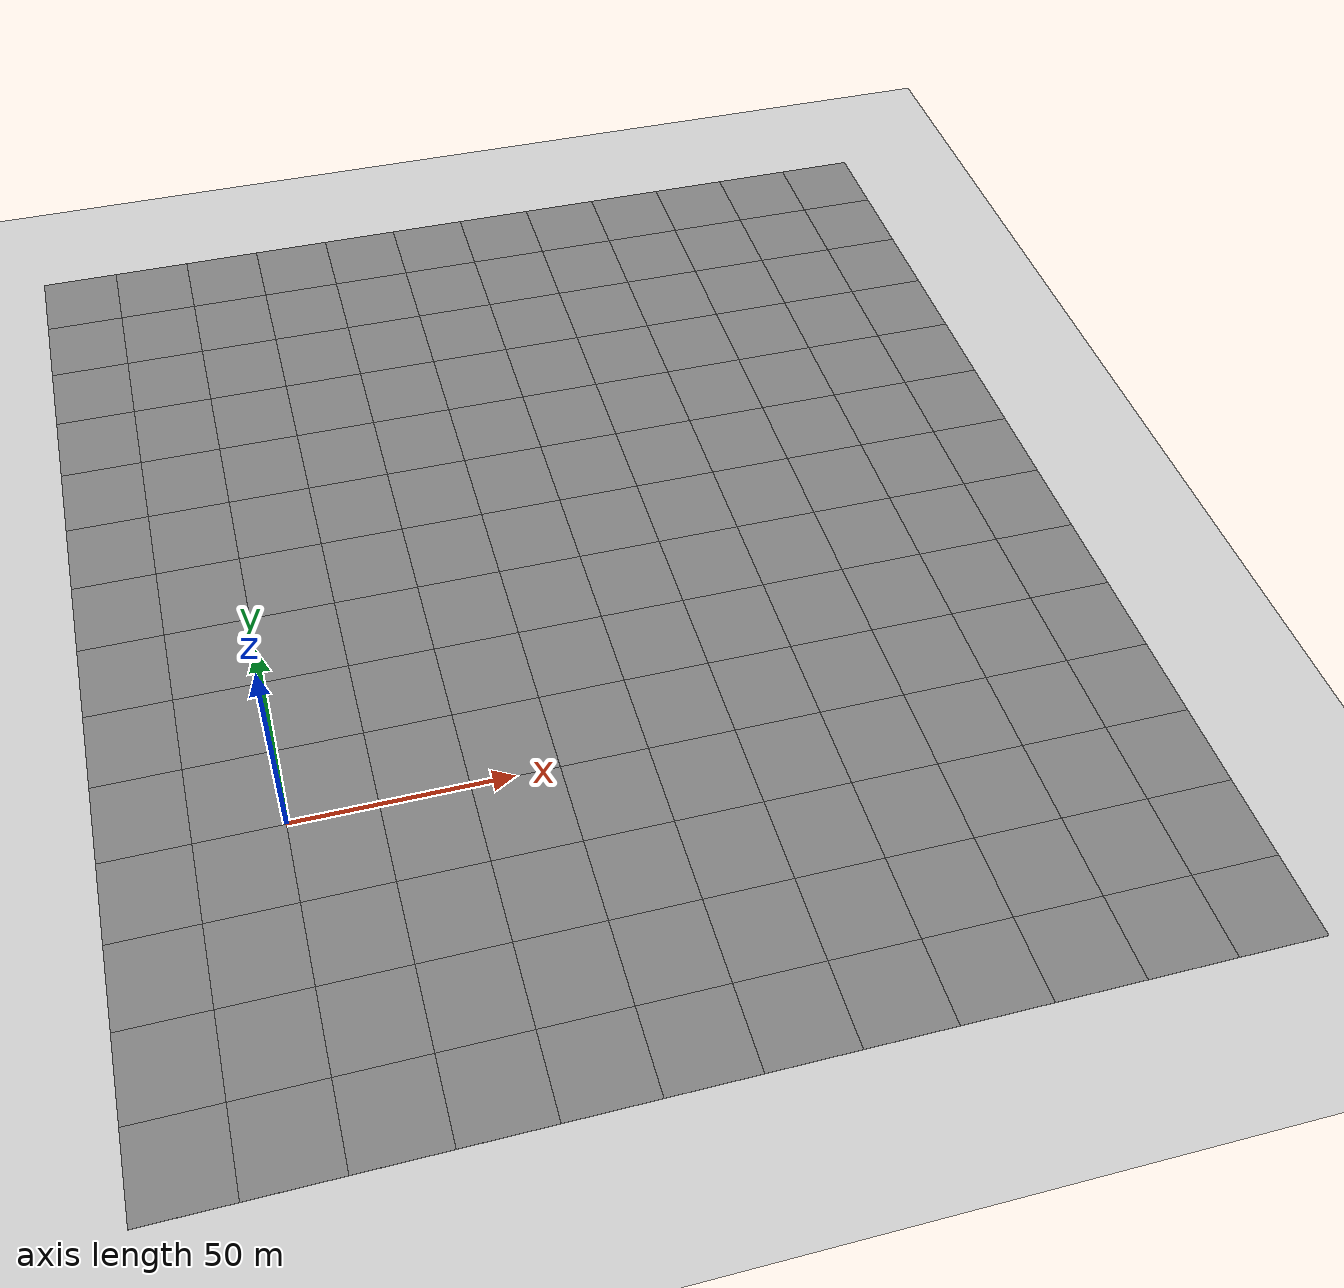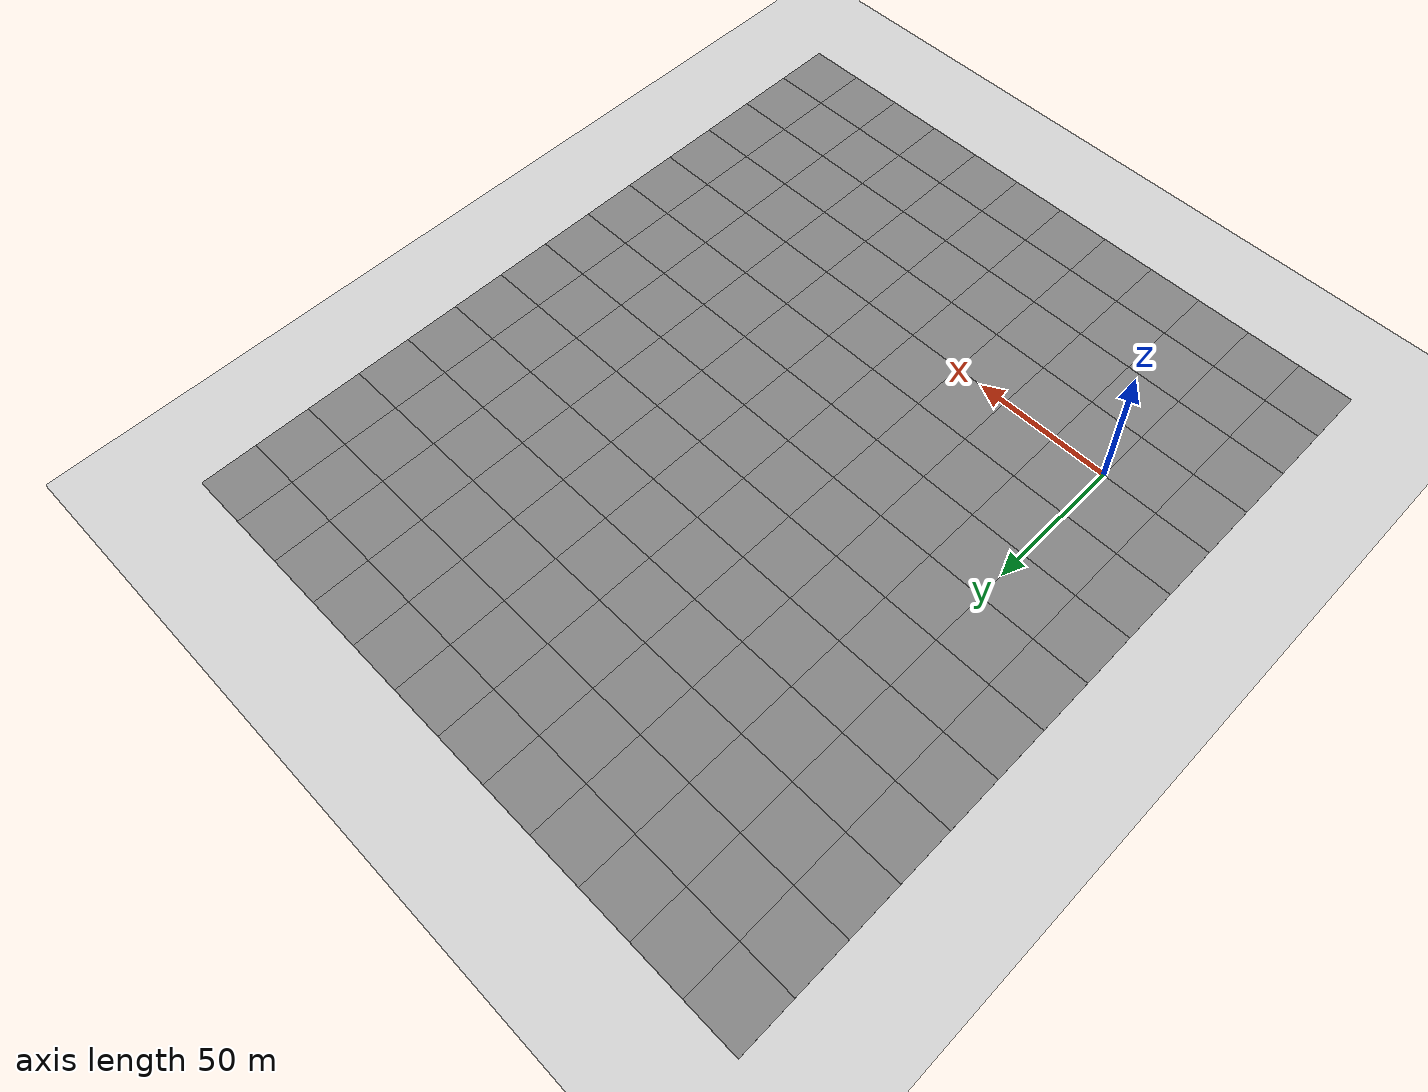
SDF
<sdf version="1.9">
 <world name="test_city_4">
  <model name="ground_plane">
   <static>true</static>
   <link name="link">
    <collision name="collision">
     <geometry><plane><normal>0 0 1</normal><size>500 500</size></plane></geometry>
    </collision>
    <visual name="visual">
     <geometry><plane><normal>0 0 1</normal><size>500 500</size></plane></geometry>
     <material>
      <ambient>0.8 0.8 0.8 1</ambient>
      <diffuse>0.8 0.8 0.8 1</diffuse>
      <specular>0.8 0.8 0.8 1</specular>
     </material>
    </visual>
   </link>
  </model>
  <light name="sun" type="directional">
   <pose>0 0 10 0 0 0</pose>
   <diffuse>0.8 0.8 0.8 1</diffuse>
   <specular>0.2 0.2 0.2 1</specular>
   <attenuation>
    <range>1000</range>
    <constant>0.9</constant>
    <linear>0.01</linear>
    <quadratic>0.001</quadratic>
   </attenuation>
   <direction>-0.5 0.1 -0.9</direction>
  </light>
  <physics type="ode">
   <max_step_size>0.004</max_step_size>
   <real_time_factor>1</real_time_factor>
   <real_time_update_rate>250</real_time_update_rate>
  </physics>
  <magnetic_field>6e-06 2.3e-05 -4.2e-05</magnetic_field>
  <gravity>0 0 -9.8066</gravity>
  <scene><ambient>0.4 0.4 0.4 1</ambient><background>0.7 0.7 0.7 1</background><shadows>1</shadows></scene>
  <spherical_coordinates>
   <surface_model>EARTH_WGS84</surface_model>
   <world_frame_orientation>ENU</world_frame_orientation>
   <latitude_deg>0</latitude_deg>
   <longitude_deg>0</longitude_deg>
   <elevation>0</elevation>
  </spherical_coordinates>
  <model name="asphalt_plane">
   <static>1</static>
   <link name="link">
    <collision name="collision"><geometry><box><size>20 20 0.1</size></box></geometry></collision>
    <visual name="visual">
     <cast_shadows>0</cast_shadows>
     <geometry><box><size>20 20 0.1</size></box></geometry>
     <material>
      <ambient>0.5 0.5 0.5 1</ambient>
      <diffuse>0.5 0.5 0.5 1</diffuse>
      <specular>0.2 0.2 0.2 1</specular>
      <pbr><metal><albedo_map>model://asphalt_plane/materials/textures/tarmac.png</albedo_map></metal></pbr>
     </material>
    </visual>
   </link>
   <pose>-30 -30 0 0 0 0</pose>
  </model>
  <model name="asphalt_plane_1">
   <static>1</static>
   <link name="link">
    <collision name="collision"><geometry><box><size>20 20 0.1</size></box></geometry></collision>
    <visual name="visual">
     <cast_shadows>0</cast_shadows>
     <geometry><box><size>20 20 0.1</size></box></geometry>
     <material>
      <ambient>0.5 0.5 0.5 1</ambient>
      <diffuse>0.5 0.5 0.5 1</diffuse>
      <specular>0.2 0.2 0.2 1</specular>
      <pbr><metal><albedo_map>model://asphalt_plane/materials/textures/tarmac.png</albedo_map></metal></pbr>
     </material>
    </visual>
   </link>
   <pose>-30 -10 0 0 0 0</pose>
  </model>
  <model name="asphalt_plane_2">
   <static>1</static>
   <link name="link">
    <collision name="collision"><geometry><box><size>20 20 0.1</size></box></geometry></collision>
    <visual name="visual">
     <cast_shadows>0</cast_shadows>
     <geometry><box><size>20 20 0.1</size></box></geometry>
     <material>
      <ambient>0.5 0.5 0.5 1</ambient>
      <diffuse>0.5 0.5 0.5 1</diffuse>
      <specular>0.2 0.2 0.2 1</specular>
      <pbr><metal><albedo_map>model://asphalt_plane/materials/textures/tarmac.png</albedo_map></metal></pbr>
     </material>
    </visual>
   </link>
   <pose>-30 10 0 0 0 0</pose>
  </model>
  <model name="asphalt_plane_3">
   <static>1</static>
   <link name="link">
    <collision name="collision"><geometry><box><size>20 20 0.1</size></box></geometry></collision>
    <visual name="visual">
     <cast_shadows>0</cast_shadows>
     <geometry><box><size>20 20 0.1</size></box></geometry>
     <material>
      <ambient>0.5 0.5 0.5 1</ambient>
      <diffuse>0.5 0.5 0.5 1</diffuse>
      <specular>0.2 0.2 0.2 1</specular>
      <pbr><metal><albedo_map>model://asphalt_plane/materials/textures/tarmac.png</albedo_map></metal></pbr>
     </material>
    </visual>
   </link>
   <pose>-30 30 0 0 0 0</pose>
  </model>
  <model name="asphalt_plane_4">
   <static>1</static>
   <link name="link">
    <collision name="collision"><geometry><box><size>20 20 0.1</size></box></geometry></collision>
    <visual name="visual">
     <cast_shadows>0</cast_shadows>
     <geometry><box><size>20 20 0.1</size></box></geometry>
     <material>
      <ambient>0.5 0.5 0.5 1</ambient>
      <diffuse>0.5 0.5 0.5 1</diffuse>
      <specular>0.2 0.2 0.2 1</specular>
      <pbr><metal><albedo_map>model://asphalt_plane/materials/textures/tarmac.png</albedo_map></metal></pbr>
     </material>
    </visual>
   </link>
   <pose>-30 50 0 0 0 0</pose>
  </model>
  <model name="asphalt_plane_5">
   <static>1</static>
   <link name="link">
    <collision name="collision"><geometry><box><size>20 20 0.1</size></box></geometry></collision>
    <visual name="visual">
     <cast_shadows>0</cast_shadows>
     <geometry><box><size>20 20 0.1</size></box></geometry>
     <material>
      <ambient>0.5 0.5 0.5 1</ambient>
      <diffuse>0.5 0.5 0.5 1</diffuse>
      <specular>0.2 0.2 0.2 1</specular>
      <pbr><metal><albedo_map>model://asphalt_plane/materials/textures/tarmac.png</albedo_map></metal></pbr>
     </material>
    </visual>
   </link>
   <pose>-30 70 0 0 0 0</pose>
  </model>
  <model name="asphalt_plane_6">
   <static>1</static>
   <link name="link">
    <collision name="collision"><geometry><box><size>20 20 0.1</size></box></geometry></collision>
    <visual name="visual">
     <cast_shadows>0</cast_shadows>
     <geometry><box><size>20 20 0.1</size></box></geometry>
     <material>
      <ambient>0.5 0.5 0.5 1</ambient>
      <diffuse>0.5 0.5 0.5 1</diffuse>
      <specular>0.2 0.2 0.2 1</specular>
      <pbr><metal><albedo_map>model://asphalt_plane/materials/textures/tarmac.png</albedo_map></metal></pbr>
     </material>
    </visual>
   </link>
   <pose>-30 90 0 0 0 0</pose>
  </model>
  <model name="asphalt_plane_7">
   <static>1</static>
   <link name="link">
    <collision name="collision"><geometry><box><size>20 20 0.1</size></box></geometry></collision>
    <visual name="visual">
     <cast_shadows>0</cast_shadows>
     <geometry><box><size>20 20 0.1</size></box></geometry>
     <material>
      <ambient>0.5 0.5 0.5 1</ambient>
      <diffuse>0.5 0.5 0.5 1</diffuse>
      <specular>0.2 0.2 0.2 1</specular>
      <pbr><metal><albedo_map>model://asphalt_plane/materials/textures/tarmac.png</albedo_map></metal></pbr>
     </material>
    </visual>
   </link>
   <pose>-30 110 0 0 0 0</pose>
  </model>
  <model name="asphalt_plane_8">
   <static>1</static>
   <link name="link">
    <collision name="collision"><geometry><box><size>20 20 0.1</size></box></geometry></collision>
    <visual name="visual">
     <cast_shadows>0</cast_shadows>
     <geometry><box><size>20 20 0.1</size></box></geometry>
     <material>
      <ambient>0.5 0.5 0.5 1</ambient>
      <diffuse>0.5 0.5 0.5 1</diffuse>
      <specular>0.2 0.2 0.2 1</specular>
      <pbr><metal><albedo_map>model://asphalt_plane/materials/textures/tarmac.png</albedo_map></metal></pbr>
     </material>
    </visual>
   </link>
   <pose>-30 130 0 0 0 0</pose>
  </model>
  <model name="asphalt_plane_9">
   <static>1</static>
   <link name="link">
    <collision name="collision"><geometry><box><size>20 20 0.1</size></box></geometry></collision>
    <visual name="visual">
     <cast_shadows>0</cast_shadows>
     <geometry><box><size>20 20 0.1</size></box></geometry>
     <material>
      <ambient>0.5 0.5 0.5 1</ambient>
      <diffuse>0.5 0.5 0.5 1</diffuse>
      <specular>0.2 0.2 0.2 1</specular>
      <pbr><metal><albedo_map>model://asphalt_plane/materials/textures/tarmac.png</albedo_map></metal></pbr>
     </material>
    </visual>
   </link>
   <pose>-30 150 0 0 0 0</pose>
  </model>
  <model name="asphalt_plane_10">
   <static>1</static>
   <link name="link">
    <collision name="collision"><geometry><box><size>20 20 0.1</size></box></geometry></collision>
    <visual name="visual">
     <cast_shadows>0</cast_shadows>
     <geometry><box><size>20 20 0.1</size></box></geometry>
     <material>
      <ambient>0.5 0.5 0.5 1</ambient>
      <diffuse>0.5 0.5 0.5 1</diffuse>
      <specular>0.2 0.2 0.2 1</specular>
      <pbr><metal><albedo_map>model://asphalt_plane/materials/textures/tarmac.png</albedo_map></metal></pbr>
     </material>
    </visual>
   </link>
   <pose>-30 170 0 0 0 0</pose>
  </model>
  <model name="asphalt_plane_11">
   <static>1</static>
   <link name="link">
    <collision name="collision"><geometry><box><size>20 20 0.1</size></box></geometry></collision>
    <visual name="visual">
     <cast_shadows>0</cast_shadows>
     <geometry><box><size>20 20 0.1</size></box></geometry>
     <material>
      <ambient>0.5 0.5 0.5 1</ambient>
      <diffuse>0.5 0.5 0.5 1</diffuse>
      <specular>0.2 0.2 0.2 1</specular>
      <pbr><metal><albedo_map>model://asphalt_plane/materials/textures/tarmac.png</albedo_map></metal></pbr>
     </material>
    </visual>
   </link>
   <pose>-30 190 0 0 0 0</pose>
  </model>
  <model name="asphalt_plane_12">
   <static>1</static>
   <link name="link">
    <collision name="collision"><geometry><box><size>20 20 0.1</size></box></geometry></collision>
    <visual name="visual">
     <cast_shadows>0</cast_shadows>
     <geometry><box><size>20 20 0.1</size></box></geometry>
     <material>
      <ambient>0.5 0.5 0.5 1</ambient>
      <diffuse>0.5 0.5 0.5 1</diffuse>
      <specular>0.2 0.2 0.2 1</specular>
      <pbr><metal><albedo_map>model://asphalt_plane/materials/textures/tarmac.png</albedo_map></metal></pbr>
     </material>
    </visual>
   </link>
   <pose>-10 -30 0 0 0 0</pose>
  </model>
  <model name="asphalt_plane_13">
   <static>1</static>
   <link name="link">
    <collision name="collision"><geometry><box><size>20 20 0.1</size></box></geometry></collision>
    <visual name="visual">
     <cast_shadows>0</cast_shadows>
     <geometry><box><size>20 20 0.1</size></box></geometry>
     <material>
      <ambient>0.5 0.5 0.5 1</ambient>
      <diffuse>0.5 0.5 0.5 1</diffuse>
      <specular>0.2 0.2 0.2 1</specular>
      <pbr><metal><albedo_map>model://asphalt_plane/materials/textures/tarmac.png</albedo_map></metal></pbr>
     </material>
    </visual>
   </link>
   <pose>-10 -10 0 0 0 0</pose>
  </model>
  <model name="asphalt_plane_14">
   <static>1</static>
   <link name="link">
    <collision name="collision"><geometry><box><size>20 20 0.1</size></box></geometry></collision>
    <visual name="visual">
     <cast_shadows>0</cast_shadows>
     <geometry><box><size>20 20 0.1</size></box></geometry>
     <material>
      <ambient>0.5 0.5 0.5 1</ambient>
      <diffuse>0.5 0.5 0.5 1</diffuse>
      <specular>0.2 0.2 0.2 1</specular>
      <pbr><metal><albedo_map>model://asphalt_plane/materials/textures/tarmac.png</albedo_map></metal></pbr>
     </material>
    </visual>
   </link>
   <pose>-10 10 0 0 0 0</pose>
  </model>
  <model name="asphalt_plane_15">
   <static>1</static>
   <link name="link">
    <collision name="collision"><geometry><box><size>20 20 0.1</size></box></geometry></collision>
    <visual name="visual">
     <cast_shadows>0</cast_shadows>
     <geometry><box><size>20 20 0.1</size></box></geometry>
     <material>
      <ambient>0.5 0.5 0.5 1</ambient>
      <diffuse>0.5 0.5 0.5 1</diffuse>
      <specular>0.2 0.2 0.2 1</specular>
      <pbr><metal><albedo_map>model://asphalt_plane/materials/textures/tarmac.png</albedo_map></metal></pbr>
     </material>
    </visual>
   </link>
   <pose>-10 30 0 0 0 0</pose>
  </model>
  <model name="asphalt_plane_16">
   <static>1</static>
   <link name="link">
    <collision name="collision"><geometry><box><size>20 20 0.1</size></box></geometry></collision>
    <visual name="visual">
     <cast_shadows>0</cast_shadows>
     <geometry><box><size>20 20 0.1</size></box></geometry>
     <material>
      <ambient>0.5 0.5 0.5 1</ambient>
      <diffuse>0.5 0.5 0.5 1</diffuse>
      <specular>0.2 0.2 0.2 1</specular>
      <pbr><metal><albedo_map>model://asphalt_plane/materials/textures/tarmac.png</albedo_map></metal></pbr>
     </material>
    </visual>
   </link>
   <pose>-10 50 0 0 0 0</pose>
  </model>
  <model name="asphalt_plane_17">
   <static>1</static>
   <link name="link">
    <collision name="collision"><geometry><box><size>20 20 0.1</size></box></geometry></collision>
    <visual name="visual">
     <cast_shadows>0</cast_shadows>
     <geometry><box><size>20 20 0.1</size></box></geometry>
     <material>
      <ambient>0.5 0.5 0.5 1</ambient>
      <diffuse>0.5 0.5 0.5 1</diffuse>
      <specular>0.2 0.2 0.2 1</specular>
      <pbr><metal><albedo_map>model://asphalt_plane/materials/textures/tarmac.png</albedo_map></metal></pbr>
     </material>
    </visual>
   </link>
   <pose>-10 70 0 0 0 0</pose>
  </model>
  <model name="asphalt_plane_18">
   <static>1</static>
   <link name="link">
    <collision name="collision"><geometry><box><size>20 20 0.1</size></box></geometry></collision>
    <visual name="visual">
     <cast_shadows>0</cast_shadows>
     <geometry><box><size>20 20 0.1</size></box></geometry>
     <material>
      <ambient>0.5 0.5 0.5 1</ambient>
      <diffuse>0.5 0.5 0.5 1</diffuse>
      <specular>0.2 0.2 0.2 1</specular>
      <pbr><metal><albedo_map>model://asphalt_plane/materials/textures/tarmac.png</albedo_map></metal></pbr>
     </material>
    </visual>
   </link>
   <pose>-10 90 0 0 0 0</pose>
  </model>
  <model name="asphalt_plane_19">
   <static>1</static>
   <link name="link">
    <collision name="collision"><geometry><box><size>20 20 0.1</size></box></geometry></collision>
    <visual name="visual">
     <cast_shadows>0</cast_shadows>
     <geometry><box><size>20 20 0.1</size></box></geometry>
     <material>
      <ambient>0.5 0.5 0.5 1</ambient>
      <diffuse>0.5 0.5 0.5 1</diffuse>
      <specular>0.2 0.2 0.2 1</specular>
      <pbr><metal><albedo_map>model://asphalt_plane/materials/textures/tarmac.png</albedo_map></metal></pbr>
     </material>
    </visual>
   </link>
   <pose>-10 110 0 0 0 0</pose>
  </model>
  <model name="asphalt_plane_20">
   <static>1</static>
   <link name="link">
    <collision name="collision"><geometry><box><size>20 20 0.1</size></box></geometry></collision>
    <visual name="visual">
     <cast_shadows>0</cast_shadows>
     <geometry><box><size>20 20 0.1</size></box></geometry>
     <material>
      <ambient>0.5 0.5 0.5 1</ambient>
      <diffuse>0.5 0.5 0.5 1</diffuse>
      <specular>0.2 0.2 0.2 1</specular>
      <pbr><metal><albedo_map>model://asphalt_plane/materials/textures/tarmac.png</albedo_map></metal></pbr>
     </material>
    </visual>
   </link>
   <pose>-10 130 0 0 0 0</pose>
  </model>
  <model name="asphalt_plane_21">
   <static>1</static>
   <link name="link">
    <collision name="collision"><geometry><box><size>20 20 0.1</size></box></geometry></collision>
    <visual name="visual">
     <cast_shadows>0</cast_shadows>
     <geometry><box><size>20 20 0.1</size></box></geometry>
     <material>
      <ambient>0.5 0.5 0.5 1</ambient>
      <diffuse>0.5 0.5 0.5 1</diffuse>
      <specular>0.2 0.2 0.2 1</specular>
      <pbr><metal><albedo_map>model://asphalt_plane/materials/textures/tarmac.png</albedo_map></metal></pbr>
     </material>
    </visual>
   </link>
   <pose>-10 150 0 0 0 0</pose>
  </model>
  <model name="asphalt_plane_22">
   <static>1</static>
   <link name="link">
    <collision name="collision"><geometry><box><size>20 20 0.1</size></box></geometry></collision>
    <visual name="visual">
     <cast_shadows>0</cast_shadows>
     <geometry><box><size>20 20 0.1</size></box></geometry>
     <material>
      <ambient>0.5 0.5 0.5 1</ambient>
      <diffuse>0.5 0.5 0.5 1</diffuse>
      <specular>0.2 0.2 0.2 1</specular>
      <pbr><metal><albedo_map>model://asphalt_plane/materials/textures/tarmac.png</albedo_map></metal></pbr>
     </material>
    </visual>
   </link>
   <pose>-10 170 0 0 0 0</pose>
  </model>
  <model name="asphalt_plane_23">
   <static>1</static>
   <link name="link">
    <collision name="collision"><geometry><box><size>20 20 0.1</size></box></geometry></collision>
    <visual name="visual">
     <cast_shadows>0</cast_shadows>
     <geometry><box><size>20 20 0.1</size></box></geometry>
     <material>
      <ambient>0.5 0.5 0.5 1</ambient>
      <diffuse>0.5 0.5 0.5 1</diffuse>
      <specular>0.2 0.2 0.2 1</specular>
      <pbr><metal><albedo_map>model://asphalt_plane/materials/textures/tarmac.png</albedo_map></metal></pbr>
     </material>
    </visual>
   </link>
   <pose>-10 190 0 0 0 0</pose>
  </model>
  <model name="asphalt_plane_24">
   <static>1</static>
   <link name="link">
    <collision name="collision"><geometry><box><size>20 20 0.1</size></box></geometry></collision>
    <visual name="visual">
     <cast_shadows>0</cast_shadows>
     <geometry><box><size>20 20 0.1</size></box></geometry>
     <material>
      <ambient>0.5 0.5 0.5 1</ambient>
      <diffuse>0.5 0.5 0.5 1</diffuse>
      <specular>0.2 0.2 0.2 1</specular>
      <pbr><metal><albedo_map>model://asphalt_plane/materials/textures/tarmac.png</albedo_map></metal></pbr>
     </material>
    </visual>
   </link>
   <pose>10 -30 0 0 0 0</pose>
  </model>
  <model name="asphalt_plane_25">
   <static>1</static>
   <link name="link">
    <collision name="collision"><geometry><box><size>20 20 0.1</size></box></geometry></collision>
    <visual name="visual">
     <cast_shadows>0</cast_shadows>
     <geometry><box><size>20 20 0.1</size></box></geometry>
     <material>
      <ambient>0.5 0.5 0.5 1</ambient>
      <diffuse>0.5 0.5 0.5 1</diffuse>
      <specular>0.2 0.2 0.2 1</specular>
      <pbr><metal><albedo_map>model://asphalt_plane/materials/textures/tarmac.png</albedo_map></metal></pbr>
     </material>
    </visual>
   </link>
   <pose>10 -10 0 0 0 0</pose>
  </model>
  <model name="asphalt_plane_26">
   <static>1</static>
   <link name="link">
    <collision name="collision"><geometry><box><size>20 20 0.1</size></box></geometry></collision>
    <visual name="visual">
     <cast_shadows>0</cast_shadows>
     <geometry><box><size>20 20 0.1</size></box></geometry>
     <material>
      <ambient>0.5 0.5 0.5 1</ambient>
      <diffuse>0.5 0.5 0.5 1</diffuse>
      <specular>0.2 0.2 0.2 1</specular>
      <pbr><metal><albedo_map>model://asphalt_plane/materials/textures/tarmac.png</albedo_map></metal></pbr>
     </material>
    </visual>
   </link>
   <pose>10 10 0 0 0 0</pose>
  </model>
  <model name="asphalt_plane_27">
   <static>1</static>
   <link name="link">
    <collision name="collision"><geometry><box><size>20 20 0.1</size></box></geometry></collision>
    <visual name="visual">
     <cast_shadows>0</cast_shadows>
     <geometry><box><size>20 20 0.1</size></box></geometry>
     <material>
      <ambient>0.5 0.5 0.5 1</ambient>
      <diffuse>0.5 0.5 0.5 1</diffuse>
      <specular>0.2 0.2 0.2 1</specular>
      <pbr><metal><albedo_map>model://asphalt_plane/materials/textures/tarmac.png</albedo_map></metal></pbr>
     </material>
    </visual>
   </link>
   <pose>10 30 0 0 0 0</pose>
  </model>
  <model name="asphalt_plane_28">
   <static>1</static>
   <link name="link">
    <collision name="collision"><geometry><box><size>20 20 0.1</size></box></geometry></collision>
    <visual name="visual">
     <cast_shadows>0</cast_shadows>
     <geometry><box><size>20 20 0.1</size></box></geometry>
     <material>
      <ambient>0.5 0.5 0.5 1</ambient>
      <diffuse>0.5 0.5 0.5 1</diffuse>
      <specular>0.2 0.2 0.2 1</specular>
      <pbr><metal><albedo_map>model://asphalt_plane/materials/textures/tarmac.png</albedo_map></metal></pbr>
     </material>
    </visual>
   </link>
   <pose>10 50 0 0 0 0</pose>
  </model>
  <model name="asphalt_plane_29">
   <static>1</static>
   <link name="link">
    <collision name="collision"><geometry><box><size>20 20 0.1</size></box></geometry></collision>
    <visual name="visual">
     <cast_shadows>0</cast_shadows>
     <geometry><box><size>20 20 0.1</size></box></geometry>
     <material>
      <ambient>0.5 0.5 0.5 1</ambient>
      <diffuse>0.5 0.5 0.5 1</diffuse>
      <specular>0.2 0.2 0.2 1</specular>
      <pbr><metal><albedo_map>model://asphalt_plane/materials/textures/tarmac.png</albedo_map></metal></pbr>
     </material>
    </visual>
   </link>
   <pose>10 70 0 0 0 0</pose>
  </model>
  <model name="asphalt_plane_30">
   <static>1</static>
   <link name="link">
    <collision name="collision"><geometry><box><size>20 20 0.1</size></box></geometry></collision>
    <visual name="visual">
     <cast_shadows>0</cast_shadows>
     <geometry><box><size>20 20 0.1</size></box></geometry>
     <material>
      <ambient>0.5 0.5 0.5 1</ambient>
      <diffuse>0.5 0.5 0.5 1</diffuse>
      <specular>0.2 0.2 0.2 1</specular>
      <pbr><metal><albedo_map>model://asphalt_plane/materials/textures/tarmac.png</albedo_map></metal></pbr>
     </material>
    </visual>
   </link>
   <pose>10 90 0 0 0 0</pose>
  </model>
  <model name="asphalt_plane_31">
   <static>1</static>
   <link name="link">
    <collision name="collision"><geometry><box><size>20 20 0.1</size></box></geometry></collision>
    <visual name="visual">
     <cast_shadows>0</cast_shadows>
     <geometry><box><size>20 20 0.1</size></box></geometry>
     <material>
      <ambient>0.5 0.5 0.5 1</ambient>
      <diffuse>0.5 0.5 0.5 1</diffuse>
      <specular>0.2 0.2 0.2 1</specular>
      <pbr><metal><albedo_map>model://asphalt_plane/materials/textures/tarmac.png</albedo_map></metal></pbr>
     </material>
    </visual>
   </link>
   <pose>10 110 0 0 0 0</pose>
  </model>
  <model name="asphalt_plane_32">
   <static>1</static>
   <link name="link">
    <collision name="collision"><geometry><box><size>20 20 0.1</size></box></geometry></collision>
    <visual name="visual">
     <cast_shadows>0</cast_shadows>
     <geometry><box><size>20 20 0.1</size></box></geometry>
     <material>
      <ambient>0.5 0.5 0.5 1</ambient>
      <diffuse>0.5 0.5 0.5 1</diffuse>
      <specular>0.2 0.2 0.2 1</specular>
      <pbr><metal><albedo_map>model://asphalt_plane/materials/textures/tarmac.png</albedo_map></metal></pbr>
     </material>
    </visual>
   </link>
   <pose>10 130 0 0 0 0</pose>
  </model>
  <model name="asphalt_plane_33">
   <static>1</static>
   <link name="link">
    <collision name="collision"><geometry><box><size>20 20 0.1</size></box></geometry></collision>
    <visual name="visual">
     <cast_shadows>0</cast_shadows>
     <geometry><box><size>20 20 0.1</size></box></geometry>
     <material>
      <ambient>0.5 0.5 0.5 1</ambient>
      <diffuse>0.5 0.5 0.5 1</diffuse>
      <specular>0.2 0.2 0.2 1</specular>
      <pbr><metal><albedo_map>model://asphalt_plane/materials/textures/tarmac.png</albedo_map></metal></pbr>
     </material>
    </visual>
   </link>
   <pose>10 150 0 0 0 0</pose>
  </model>
  <model name="asphalt_plane_34">
   <static>1</static>
   <link name="link">
    <collision name="collision"><geometry><box><size>20 20 0.1</size></box></geometry></collision>
    <visual name="visual">
     <cast_shadows>0</cast_shadows>
     <geometry><box><size>20 20 0.1</size></box></geometry>
     <material>
      <ambient>0.5 0.5 0.5 1</ambient>
      <diffuse>0.5 0.5 0.5 1</diffuse>
      <specular>0.2 0.2 0.2 1</specular>
      <pbr><metal><albedo_map>model://asphalt_plane/materials/textures/tarmac.png</albedo_map></metal></pbr>
     </material>
    </visual>
   </link>
   <pose>10 170 0 0 0 0</pose>
  </model>
  <model name="asphalt_plane_35">
   <static>1</static>
   <link name="link">
    <collision name="collision"><geometry><box><size>20 20 0.1</size></box></geometry></collision>
    <visual name="visual">
     <cast_shadows>0</cast_shadows>
     <geometry><box><size>20 20 0.1</size></box></geometry>
     <material>
      <ambient>0.5 0.5 0.5 1</ambient>
      <diffuse>0.5 0.5 0.5 1</diffuse>
      <specular>0.2 0.2 0.2 1</specular>
      <pbr><metal><albedo_map>model://asphalt_plane/materials/textures/tarmac.png</albedo_map></metal></pbr>
     </material>
    </visual>
   </link>
   <pose>10 190 0 0 0 0</pose>
  </model>
  <model name="asphalt_plane_36">
   <static>1</static>
   <link name="link">
    <collision name="collision"><geometry><box><size>20 20 0.1</size></box></geometry></collision>
    <visual name="visual">
     <cast_shadows>0</cast_shadows>
     <geometry><box><size>20 20 0.1</size></box></geometry>
     <material>
      <ambient>0.5 0.5 0.5 1</ambient>
      <diffuse>0.5 0.5 0.5 1</diffuse>
      <specular>0.2 0.2 0.2 1</specular>
      <pbr><metal><albedo_map>model://asphalt_plane/materials/textures/tarmac.png</albedo_map></metal></pbr>
     </material>
    </visual>
   </link>
   <pose>30 -30 0 0 0 0</pose>
  </model>
  <model name="asphalt_plane_37">
   <static>1</static>
   <link name="link">
    <collision name="collision"><geometry><box><size>20 20 0.1</size></box></geometry></collision>
    <visual name="visual">
     <cast_shadows>0</cast_shadows>
     <geometry><box><size>20 20 0.1</size></box></geometry>
     <material>
      <ambient>0.5 0.5 0.5 1</ambient>
      <diffuse>0.5 0.5 0.5 1</diffuse>
      <specular>0.2 0.2 0.2 1</specular>
      <pbr><metal><albedo_map>model://asphalt_plane/materials/textures/tarmac.png</albedo_map></metal></pbr>
     </material>
    </visual>
   </link>
   <pose>30 -10 0 0 0 0</pose>
  </model>
  <model name="asphalt_plane_38">
   <static>1</static>
   <link name="link">
    <collision name="collision"><geometry><box><size>20 20 0.1</size></box></geometry></collision>
    <visual name="visual">
     <cast_shadows>0</cast_shadows>
     <geometry><box><size>20 20 0.1</size></box></geometry>
     <material>
      <ambient>0.5 0.5 0.5 1</ambient>
      <diffuse>0.5 0.5 0.5 1</diffuse>
      <specular>0.2 0.2 0.2 1</specular>
      <pbr><metal><albedo_map>model://asphalt_plane/materials/textures/tarmac.png</albedo_map></metal></pbr>
     </material>
    </visual>
   </link>
   <pose>30 10 0 0 0 0</pose>
  </model>
  <model name="asphalt_plane_39">
   <static>1</static>
   <link name="link">
    <collision name="collision"><geometry><box><size>20 20 0.1</size></box></geometry></collision>
    <visual name="visual">
     <cast_shadows>0</cast_shadows>
     <geometry><box><size>20 20 0.1</size></box></geometry>
     <material>
      <ambient>0.5 0.5 0.5 1</ambient>
      <diffuse>0.5 0.5 0.5 1</diffuse>
      <specular>0.2 0.2 0.2 1</specular>
      <pbr><metal><albedo_map>model://asphalt_plane/materials/textures/tarmac.png</albedo_map></metal></pbr>
     </material>
    </visual>
   </link>
   <pose>30 30 0 0 0 0</pose>
  </model>
  <model name="asphalt_plane_40">
   <static>1</static>
   <link name="link">
    <collision name="collision"><geometry><box><size>20 20 0.1</size></box></geometry></collision>
    <visual name="visual">
     <cast_shadows>0</cast_shadows>
     <geometry><box><size>20 20 0.1</size></box></geometry>
     <material>
      <ambient>0.5 0.5 0.5 1</ambient>
      <diffuse>0.5 0.5 0.5 1</diffuse>
      <specular>0.2 0.2 0.2 1</specular>
      <pbr><metal><albedo_map>model://asphalt_plane/materials/textures/tarmac.png</albedo_map></metal></pbr>
     </material>
    </visual>
   </link>
   <pose>30 50 0 0 0 0</pose>
  </model>
  <model name="asphalt_plane_41">
   <static>1</static>
   <link name="link">
    <collision name="collision"><geometry><box><size>20 20 0.1</size></box></geometry></collision>
    <visual name="visual">
     <cast_shadows>0</cast_shadows>
     <geometry><box><size>20 20 0.1</size></box></geometry>
     <material>
      <ambient>0.5 0.5 0.5 1</ambient>
      <diffuse>0.5 0.5 0.5 1</diffuse>
      <specular>0.2 0.2 0.2 1</specular>
      <pbr><metal><albedo_map>model://asphalt_plane/materials/textures/tarmac.png</albedo_map></metal></pbr>
     </material>
    </visual>
   </link>
   <pose>30 70 0 0 0 0</pose>
  </model>
  <model name="asphalt_plane_42">
   <static>1</static>
   <link name="link">
    <collision name="collision"><geometry><box><size>20 20 0.1</size></box></geometry></collision>
    <visual name="visual">
     <cast_shadows>0</cast_shadows>
     <geometry><box><size>20 20 0.1</size></box></geometry>
     <material>
      <ambient>0.5 0.5 0.5 1</ambient>
      <diffuse>0.5 0.5 0.5 1</diffuse>
      <specular>0.2 0.2 0.2 1</specular>
      <pbr><metal><albedo_map>model://asphalt_plane/materials/textures/tarmac.png</albedo_map></metal></pbr>
     </material>
    </visual>
   </link>
   <pose>30 90 0 0 0 0</pose>
  </model>
  <model name="asphalt_plane_43">
   <static>1</static>
   <link name="link">
    <collision name="collision"><geometry><box><size>20 20 0.1</size></box></geometry></collision>
    <visual name="visual">
     <cast_shadows>0</cast_shadows>
     <geometry><box><size>20 20 0.1</size></box></geometry>
     <material>
      <ambient>0.5 0.5 0.5 1</ambient>
      <diffuse>0.5 0.5 0.5 1</diffuse>
      <specular>0.2 0.2 0.2 1</specular>
      <pbr><metal><albedo_map>model://asphalt_plane/materials/textures/tarmac.png</albedo_map></metal></pbr>
     </material>
    </visual>
   </link>
   <pose>30 110 0 0 0 0</pose>
  </model>
  <model name="asphalt_plane_44">
   <static>1</static>
   <link name="link">
    <collision name="collision"><geometry><box><size>20 20 0.1</size></box></geometry></collision>
    <visual name="visual">
     <cast_shadows>0</cast_shadows>
     <geometry><box><size>20 20 0.1</size></box></geometry>
     <material>
      <ambient>0.5 0.5 0.5 1</ambient>
      <diffuse>0.5 0.5 0.5 1</diffuse>
      <specular>0.2 0.2 0.2 1</specular>
      <pbr><metal><albedo_map>model://asphalt_plane/materials/textures/tarmac.png</albedo_map></metal></pbr>
     </material>
    </visual>
   </link>
   <pose>30 130 0 0 0 0</pose>
  </model>
  <model name="asphalt_plane_45">
   <static>1</static>
   <link name="link">
    <collision name="collision"><geometry><box><size>20 20 0.1</size></box></geometry></collision>
    <visual name="visual">
     <cast_shadows>0</cast_shadows>
     <geometry><box><size>20 20 0.1</size></box></geometry>
     <material>
      <ambient>0.5 0.5 0.5 1</ambient>
      <diffuse>0.5 0.5 0.5 1</diffuse>
      <specular>0.2 0.2 0.2 1</specular>
      <pbr><metal><albedo_map>model://asphalt_plane/materials/textures/tarmac.png</albedo_map></metal></pbr>
     </material>
    </visual>
   </link>
   <pose>30 150 0 0 0 0</pose>
  </model>
  <model name="asphalt_plane_46">
   <static>1</static>
   <link name="link">
    <collision name="collision"><geometry><box><size>20 20 0.1</size></box></geometry></collision>
    <visual name="visual">
     <cast_shadows>0</cast_shadows>
     <geometry><box><size>20 20 0.1</size></box></geometry>
     <material>
      <ambient>0.5 0.5 0.5 1</ambient>
      <diffuse>0.5 0.5 0.5 1</diffuse>
      <specular>0.2 0.2 0.2 1</specular>
      <pbr><metal><albedo_map>model://asphalt_plane/materials/textures/tarmac.png</albedo_map></metal></pbr>
     </material>
    </visual>
   </link>
   <pose>30 170 0 0 0 0</pose>
  </model>
  <model name="asphalt_plane_47">
   <static>1</static>
   <link name="link">
    <collision name="collision"><geometry><box><size>20 20 0.1</size></box></geometry></collision>
    <visual name="visual">
     <cast_shadows>0</cast_shadows>
     <geometry><box><size>20 20 0.1</size></box></geometry>
     <material>
      <ambient>0.5 0.5 0.5 1</ambient>
      <diffuse>0.5 0.5 0.5 1</diffuse>
      <specular>0.2 0.2 0.2 1</specular>
      <pbr><metal><albedo_map>model://asphalt_plane/materials/textures/tarmac.png</albedo_map></metal></pbr>
     </material>
    </visual>
   </link>
   <pose>30 190 0 0 0 0</pose>
  </model>
  <model name="asphalt_plane_48">
   <static>1</static>
   <link name="link">
    <collision name="collision"><geometry><box><size>20 20 0.1</size></box></geometry></collision>
    <visual name="visual">
     <cast_shadows>0</cast_shadows>
     <geometry><box><size>20 20 0.1</size></box></geometry>
     <material>
      <ambient>0.5 0.5 0.5 1</ambient>
      <diffuse>0.5 0.5 0.5 1</diffuse>
      <specular>0.2 0.2 0.2 1</specular>
      <pbr><metal><albedo_map>model://asphalt_plane/materials/textures/tarmac.png</albedo_map></metal></pbr>
     </material>
    </visual>
   </link>
   <pose>50 -30 0 0 0 0</pose>
  </model>
  <model name="asphalt_plane_49">
   <static>1</static>
   <link name="link">
    <collision name="collision"><geometry><box><size>20 20 0.1</size></box></geometry></collision>
    <visual name="visual">
     <cast_shadows>0</cast_shadows>
     <geometry><box><size>20 20 0.1</size></box></geometry>
     <material>
      <ambient>0.5 0.5 0.5 1</ambient>
      <diffuse>0.5 0.5 0.5 1</diffuse>
      <specular>0.2 0.2 0.2 1</specular>
      <pbr><metal><albedo_map>model://asphalt_plane/materials/textures/tarmac.png</albedo_map></metal></pbr>
     </material>
    </visual>
   </link>
   <pose>50 -10 0 0 0 0</pose>
  </model>
  <model name="asphalt_plane_50">
   <static>1</static>
   <link name="link">
    <collision name="collision"><geometry><box><size>20 20 0.1</size></box></geometry></collision>
    <visual name="visual">
     <cast_shadows>0</cast_shadows>
     <geometry><box><size>20 20 0.1</size></box></geometry>
     <material>
      <ambient>0.5 0.5 0.5 1</ambient>
      <diffuse>0.5 0.5 0.5 1</diffuse>
      <specular>0.2 0.2 0.2 1</specular>
      <pbr><metal><albedo_map>model://asphalt_plane/materials/textures/tarmac.png</albedo_map></metal></pbr>
     </material>
    </visual>
   </link>
   <pose>50 10 0 0 0 0</pose>
  </model>
  <model name="asphalt_plane_51">
   <static>1</static>
   <link name="link">
    <collision name="collision"><geometry><box><size>20 20 0.1</size></box></geometry></collision>
    <visual name="visual">
     <cast_shadows>0</cast_shadows>
     <geometry><box><size>20 20 0.1</size></box></geometry>
     <material>
      <ambient>0.5 0.5 0.5 1</ambient>
      <diffuse>0.5 0.5 0.5 1</diffuse>
      <specular>0.2 0.2 0.2 1</specular>
      <pbr><metal><albedo_map>model://asphalt_plane/materials/textures/tarmac.png</albedo_map></metal></pbr>
     </material>
    </visual>
   </link>
   <pose>50 30 0 0 0 0</pose>
  </model>
  <model name="asphalt_plane_52">
   <static>1</static>
   <link name="link">
    <collision name="collision"><geometry><box><size>20 20 0.1</size></box></geometry></collision>
    <visual name="visual">
     <cast_shadows>0</cast_shadows>
     <geometry><box><size>20 20 0.1</size></box></geometry>
     <material>
      <ambient>0.5 0.5 0.5 1</ambient>
      <diffuse>0.5 0.5 0.5 1</diffuse>
      <specular>0.2 0.2 0.2 1</specular>
      <pbr><metal><albedo_map>model://asphalt_plane/materials/textures/tarmac.png</albedo_map></metal></pbr>
     </material>
    </visual>
   </link>
   <pose>50 50 0 0 0 0</pose>
  </model>
  <model name="asphalt_plane_53">
   <static>1</static>
   <link name="link">
    <collision name="collision"><geometry><box><size>20 20 0.1</size></box></geometry></collision>
    <visual name="visual">
     <cast_shadows>0</cast_shadows>
     <geometry><box><size>20 20 0.1</size></box></geometry>
     <material>
      <ambient>0.5 0.5 0.5 1</ambient>
      <diffuse>0.5 0.5 0.5 1</diffuse>
      <specular>0.2 0.2 0.2 1</specular>
      <pbr><metal><albedo_map>model://asphalt_plane/materials/textures/tarmac.png</albedo_map></metal></pbr>
     </material>
    </visual>
   </link>
   <pose>50 70 0 0 0 0</pose>
  </model>
  <model name="asphalt_plane_54">
   <static>1</static>
   <link name="link">
    <collision name="collision"><geometry><box><size>20 20 0.1</size></box></geometry></collision>
    <visual name="visual">
     <cast_shadows>0</cast_shadows>
     <geometry><box><size>20 20 0.1</size></box></geometry>
     <material>
      <ambient>0.5 0.5 0.5 1</ambient>
      <diffuse>0.5 0.5 0.5 1</diffuse>
      <specular>0.2 0.2 0.2 1</specular>
      <pbr><metal><albedo_map>model://asphalt_plane/materials/textures/tarmac.png</albedo_map></metal></pbr>
     </material>
    </visual>
   </link>
   <pose>50 90 0 0 0 0</pose>
  </model>
  <model name="asphalt_plane_55">
   <static>1</static>
   <link name="link">
    <collision name="collision"><geometry><box><size>20 20 0.1</size></box></geometry></collision>
    <visual name="visual">
     <cast_shadows>0</cast_shadows>
     <geometry><box><size>20 20 0.1</size></box></geometry>
     <material>
      <ambient>0.5 0.5 0.5 1</ambient>
      <diffuse>0.5 0.5 0.5 1</diffuse>
      <specular>0.2 0.2 0.2 1</specular>
      <pbr><metal><albedo_map>model://asphalt_plane/materials/textures/tarmac.png</albedo_map></metal></pbr>
     </material>
    </visual>
   </link>
   <pose>50 110 0 0 0 0</pose>
  </model>
  <model name="asphalt_plane_56">
   <static>1</static>
   <link name="link">
    <collision name="collision"><geometry><box><size>20 20 0.1</size></box></geometry></collision>
    <visual name="visual">
     <cast_shadows>0</cast_shadows>
     <geometry><box><size>20 20 0.1</size></box></geometry>
     <material>
      <ambient>0.5 0.5 0.5 1</ambient>
      <diffuse>0.5 0.5 0.5 1</diffuse>
      <specular>0.2 0.2 0.2 1</specular>
      <pbr><metal><albedo_map>model://asphalt_plane/materials/textures/tarmac.png</albedo_map></metal></pbr>
     </material>
    </visual>
   </link>
   <pose>50 130 0 0 0 0</pose>
  </model>
  <model name="asphalt_plane_57">
   <static>1</static>
   <link name="link">
    <collision name="collision"><geometry><box><size>20 20 0.1</size></box></geometry></collision>
    <visual name="visual">
     <cast_shadows>0</cast_shadows>
     <geometry><box><size>20 20 0.1</size></box></geometry>
     <material>
      <ambient>0.5 0.5 0.5 1</ambient>
      <diffuse>0.5 0.5 0.5 1</diffuse>
      <specular>0.2 0.2 0.2 1</specular>
      <pbr><metal><albedo_map>model://asphalt_plane/materials/textures/tarmac.png</albedo_map></metal></pbr>
     </material>
    </visual>
   </link>
   <pose>50 150 0 0 0 0</pose>
  </model>
  <model name="asphalt_plane_58">
   <static>1</static>
   <link name="link">
    <collision name="collision"><geometry><box><size>20 20 0.1</size></box></geometry></collision>
    <visual name="visual">
     <cast_shadows>0</cast_shadows>
     <geometry><box><size>20 20 0.1</size></box></geometry>
     <material>
      <ambient>0.5 0.5 0.5 1</ambient>
      <diffuse>0.5 0.5 0.5 1</diffuse>
      <specular>0.2 0.2 0.2 1</specular>
      <pbr><metal><albedo_map>model://asphalt_plane/materials/textures/tarmac.png</albedo_map></metal></pbr>
     </material>
    </visual>
   </link>
   <pose>50 170 0 0 0 0</pose>
  </model>
  <model name="asphalt_plane_59">
   <static>1</static>
   <link name="link">
    <collision name="collision"><geometry><box><size>20 20 0.1</size></box></geometry></collision>
    <visual name="visual">
     <cast_shadows>0</cast_shadows>
     <geometry><box><size>20 20 0.1</size></box></geometry>
     <material>
      <ambient>0.5 0.5 0.5 1</ambient>
      <diffuse>0.5 0.5 0.5 1</diffuse>
      <specular>0.2 0.2 0.2 1</specular>
      <pbr><metal><albedo_map>model://asphalt_plane/materials/textures/tarmac.png</albedo_map></metal></pbr>
     </material>
    </visual>
   </link>
   <pose>50 190 0 0 0 0</pose>
  </model>
  <model name="asphalt_plane_60">
   <static>1</static>
   <link name="link">
    <collision name="collision"><geometry><box><size>20 20 0.1</size></box></geometry></collision>
    <visual name="visual">
     <cast_shadows>0</cast_shadows>
     <geometry><box><size>20 20 0.1</size></box></geometry>
     <material>
      <ambient>0.5 0.5 0.5 1</ambient>
      <diffuse>0.5 0.5 0.5 1</diffuse>
      <specular>0.2 0.2 0.2 1</specular>
      <pbr><metal><albedo_map>model://asphalt_plane/materials/textures/tarmac.png</albedo_map></metal></pbr>
     </material>
    </visual>
   </link>
   <pose>70 -30 0 0 0 0</pose>
  </model>
  <model name="asphalt_plane_61">
   <static>1</static>
   <link name="link">
    <collision name="collision"><geometry><box><size>20 20 0.1</size></box></geometry></collision>
    <visual name="visual">
     <cast_shadows>0</cast_shadows>
     <geometry><box><size>20 20 0.1</size></box></geometry>
     <material>
      <ambient>0.5 0.5 0.5 1</ambient>
      <diffuse>0.5 0.5 0.5 1</diffuse>
      <specular>0.2 0.2 0.2 1</specular>
      <pbr><metal><albedo_map>model://asphalt_plane/materials/textures/tarmac.png</albedo_map></metal></pbr>
     </material>
    </visual>
   </link>
   <pose>70 -10 0 0 0 0</pose>
  </model>
  <model name="asphalt_plane_62">
   <static>1</static>
   <link name="link">
    <collision name="collision"><geometry><box><size>20 20 0.1</size></box></geometry></collision>
    <visual name="visual">
     <cast_shadows>0</cast_shadows>
     <geometry><box><size>20 20 0.1</size></box></geometry>
     <material>
      <ambient>0.5 0.5 0.5 1</ambient>
      <diffuse>0.5 0.5 0.5 1</diffuse>
      <specular>0.2 0.2 0.2 1</specular>
      <pbr><metal><albedo_map>model://asphalt_plane/materials/textures/tarmac.png</albedo_map></metal></pbr>
     </material>
    </visual>
   </link>
   <pose>70 10 0 0 0 0</pose>
  </model>
  <model name="asphalt_plane_63">
   <static>1</static>
   <link name="link">
    <collision name="collision"><geometry><box><size>20 20 0.1</size></box></geometry></collision>
    <visual name="visual">
     <cast_shadows>0</cast_shadows>
     <geometry><box><size>20 20 0.1</size></box></geometry>
     <material>
      <ambient>0.5 0.5 0.5 1</ambient>
      <diffuse>0.5 0.5 0.5 1</diffuse>
      <specular>0.2 0.2 0.2 1</specular>
      <pbr><metal><albedo_map>model://asphalt_plane/materials/textures/tarmac.png</albedo_map></metal></pbr>
     </material>
    </visual>
   </link>
   <pose>70 30 0 0 0 0</pose>
  </model>
  <model name="asphalt_plane_64">
   <static>1</static>
   <link name="link">
    <collision name="collision"><geometry><box><size>20 20 0.1</size></box></geometry></collision>
    <visual name="visual">
     <cast_shadows>0</cast_shadows>
     <geometry><box><size>20 20 0.1</size></box></geometry>
     <material>
      <ambient>0.5 0.5 0.5 1</ambient>
      <diffuse>0.5 0.5 0.5 1</diffuse>
      <specular>0.2 0.2 0.2 1</specular>
      <pbr><metal><albedo_map>model://asphalt_plane/materials/textures/tarmac.png</albedo_map></metal></pbr>
     </material>
    </visual>
   </link>
   <pose>70 50 0 0 0 0</pose>
  </model>
  <model name="asphalt_plane_65">
   <static>1</static>
   <link name="link">
    <collision name="collision"><geometry><box><size>20 20 0.1</size></box></geometry></collision>
    <visual name="visual">
     <cast_shadows>0</cast_shadows>
     <geometry><box><size>20 20 0.1</size></box></geometry>
     <material>
      <ambient>0.5 0.5 0.5 1</ambient>
      <diffuse>0.5 0.5 0.5 1</diffuse>
      <specular>0.2 0.2 0.2 1</specular>
      <pbr><metal><albedo_map>model://asphalt_plane/materials/textures/tarmac.png</albedo_map></metal></pbr>
     </material>
    </visual>
   </link>
   <pose>70 70 0 0 0 0</pose>
  </model>
  <model name="asphalt_plane_66">
   <static>1</static>
   <link name="link">
    <collision name="collision"><geometry><box><size>20 20 0.1</size></box></geometry></collision>
    <visual name="visual">
     <cast_shadows>0</cast_shadows>
     <geometry><box><size>20 20 0.1</size></box></geometry>
     <material>
      <ambient>0.5 0.5 0.5 1</ambient>
      <diffuse>0.5 0.5 0.5 1</diffuse>
      <specular>0.2 0.2 0.2 1</specular>
      <pbr><metal><albedo_map>model://asphalt_plane/materials/textures/tarmac.png</albedo_map></metal></pbr>
     </material>
    </visual>
   </link>
   <pose>70 90 0 0 0 0</pose>
  </model>
  <model name="asphalt_plane_67">
   <static>1</static>
   <link name="link">
    <collision name="collision"><geometry><box><size>20 20 0.1</size></box></geometry></collision>
    <visual name="visual">
     <cast_shadows>0</cast_shadows>
     <geometry><box><size>20 20 0.1</size></box></geometry>
     <material>
      <ambient>0.5 0.5 0.5 1</ambient>
      <diffuse>0.5 0.5 0.5 1</diffuse>
      <specular>0.2 0.2 0.2 1</specular>
      <pbr><metal><albedo_map>model://asphalt_plane/materials/textures/tarmac.png</albedo_map></metal></pbr>
     </material>
    </visual>
   </link>
   <pose>70 110 0 0 0 0</pose>
  </model>
  <model name="asphalt_plane_68">
   <static>1</static>
   <link name="link">
    <collision name="collision"><geometry><box><size>20 20 0.1</size></box></geometry></collision>
    <visual name="visual">
     <cast_shadows>0</cast_shadows>
     <geometry><box><size>20 20 0.1</size></box></geometry>
     <material>
      <ambient>0.5 0.5 0.5 1</ambient>
      <diffuse>0.5 0.5 0.5 1</diffuse>
      <specular>0.2 0.2 0.2 1</specular>
      <pbr><metal><albedo_map>model://asphalt_plane/materials/textures/tarmac.png</albedo_map></metal></pbr>
     </material>
    </visual>
   </link>
   <pose>70 130 0 0 0 0</pose>
  </model>
  <model name="asphalt_plane_69">
   <static>1</static>
   <link name="link">
    <collision name="collision"><geometry><box><size>20 20 0.1</size></box></geometry></collision>
    <visual name="visual">
     <cast_shadows>0</cast_shadows>
     <geometry><box><size>20 20 0.1</size></box></geometry>
     <material>
      <ambient>0.5 0.5 0.5 1</ambient>
      <diffuse>0.5 0.5 0.5 1</diffuse>
      <specular>0.2 0.2 0.2 1</specular>
      <pbr><metal><albedo_map>model://asphalt_plane/materials/textures/tarmac.png</albedo_map></metal></pbr>
     </material>
    </visual>
   </link>
   <pose>70 150 0 0 0 0</pose>
  </model>
  <model name="asphalt_plane_70">
   <static>1</static>
   <link name="link">
    <collision name="collision"><geometry><box><size>20 20 0.1</size></box></geometry></collision>
    <visual name="visual">
     <cast_shadows>0</cast_shadows>
     <geometry><box><size>20 20 0.1</size></box></geometry>
     <material>
      <ambient>0.5 0.5 0.5 1</ambient>
      <diffuse>0.5 0.5 0.5 1</diffuse>
      <specular>0.2 0.2 0.2 1</specular>
      <pbr><metal><albedo_map>model://asphalt_plane/materials/textures/tarmac.png</albedo_map></metal></pbr>
     </material>
    </visual>
   </link>
   <pose>70 170 0 0 0 0</pose>
  </model>
  <model name="asphalt_plane_71">
   <static>1</static>
   <link name="link">
    <collision name="collision"><geometry><box><size>20 20 0.1</size></box></geometry></collision>
    <visual name="visual">
     <cast_shadows>0</cast_shadows>
     <geometry><box><size>20 20 0.1</size></box></geometry>
     <material>
      <ambient>0.5 0.5 0.5 1</ambient>
      <diffuse>0.5 0.5 0.5 1</diffuse>
      <specular>0.2 0.2 0.2 1</specular>
      <pbr><metal><albedo_map>model://asphalt_plane/materials/textures/tarmac.png</albedo_map></metal></pbr>
     </material>
    </visual>
   </link>
   <pose>70 190 0 0 0 0</pose>
  </model>
  <model name="asphalt_plane_72">
   <static>1</static>
   <link name="link">
    <collision name="collision"><geometry><box><size>20 20 0.1</size></box></geometry></collision>
    <visual name="visual">
     <cast_shadows>0</cast_shadows>
     <geometry><box><size>20 20 0.1</size></box></geometry>
     <material>
      <ambient>0.5 0.5 0.5 1</ambient>
      <diffuse>0.5 0.5 0.5 1</diffuse>
      <specular>0.2 0.2 0.2 1</specular>
      <pbr><metal><albedo_map>model://asphalt_plane/materials/textures/tarmac.png</albedo_map></metal></pbr>
     </material>
    </visual>
   </link>
   <pose>90 -30 0 0 0 0</pose>
  </model>
  <model name="asphalt_plane_73">
   <static>1</static>
   <link name="link">
    <collision name="collision"><geometry><box><size>20 20 0.1</size></box></geometry></collision>
    <visual name="visual">
     <cast_shadows>0</cast_shadows>
     <geometry><box><size>20 20 0.1</size></box></geometry>
     <material>
      <ambient>0.5 0.5 0.5 1</ambient>
      <diffuse>0.5 0.5 0.5 1</diffuse>
      <specular>0.2 0.2 0.2 1</specular>
      <pbr><metal><albedo_map>model://asphalt_plane/materials/textures/tarmac.png</albedo_map></metal></pbr>
     </material>
    </visual>
   </link>
   <pose>90 -10 0 0 0 0</pose>
  </model>
  <model name="asphalt_plane_74">
   <static>1</static>
   <link name="link">
    <collision name="collision"><geometry><box><size>20 20 0.1</size></box></geometry></collision>
    <visual name="visual">
     <cast_shadows>0</cast_shadows>
     <geometry><box><size>20 20 0.1</size></box></geometry>
     <material>
      <ambient>0.5 0.5 0.5 1</ambient>
      <diffuse>0.5 0.5 0.5 1</diffuse>
      <specular>0.2 0.2 0.2 1</specular>
      <pbr><metal><albedo_map>model://asphalt_plane/materials/textures/tarmac.png</albedo_map></metal></pbr>
     </material>
    </visual>
   </link>
   <pose>90 10 0 0 0 0</pose>
  </model>
  <model name="asphalt_plane_75">
   <static>1</static>
   <link name="link">
    <collision name="collision"><geometry><box><size>20 20 0.1</size></box></geometry></collision>
    <visual name="visual">
     <cast_shadows>0</cast_shadows>
     <geometry><box><size>20 20 0.1</size></box></geometry>
     <material>
      <ambient>0.5 0.5 0.5 1</ambient>
      <diffuse>0.5 0.5 0.5 1</diffuse>
      <specular>0.2 0.2 0.2 1</specular>
      <pbr><metal><albedo_map>model://asphalt_plane/materials/textures/tarmac.png</albedo_map></metal></pbr>
     </material>
    </visual>
   </link>
   <pose>90 30 0 0 0 0</pose>
  </model>
  <model name="asphalt_plane_76">
   <static>1</static>
   <link name="link">
    <collision name="collision"><geometry><box><size>20 20 0.1</size></box></geometry></collision>
    <visual name="visual">
     <cast_shadows>0</cast_shadows>
     <geometry><box><size>20 20 0.1</size></box></geometry>
     <material>
      <ambient>0.5 0.5 0.5 1</ambient>
      <diffuse>0.5 0.5 0.5 1</diffuse>
      <specular>0.2 0.2 0.2 1</specular>
      <pbr><metal><albedo_map>model://asphalt_plane/materials/textures/tarmac.png</albedo_map></metal></pbr>
     </material>
    </visual>
   </link>
   <pose>90 50 0 0 0 0</pose>
  </model>
  <model name="asphalt_plane_77">
   <static>1</static>
   <link name="link">
    <collision name="collision"><geometry><box><size>20 20 0.1</size></box></geometry></collision>
    <visual name="visual">
     <cast_shadows>0</cast_shadows>
     <geometry><box><size>20 20 0.1</size></box></geometry>
     <material>
      <ambient>0.5 0.5 0.5 1</ambient>
      <diffuse>0.5 0.5 0.5 1</diffuse>
      <specular>0.2 0.2 0.2 1</specular>
      <pbr><metal><albedo_map>model://asphalt_plane/materials/textures/tarmac.png</albedo_map></metal></pbr>
     </material>
    </visual>
   </link>
   <pose>90 70 0 0 0 0</pose>
  </model>
  <model name="asphalt_plane_78">
   <static>1</static>
   <link name="link">
    <collision name="collision"><geometry><box><size>20 20 0.1</size></box></geometry></collision>
    <visual name="visual">
     <cast_shadows>0</cast_shadows>
     <geometry><box><size>20 20 0.1</size></box></geometry>
     <material>
      <ambient>0.5 0.5 0.5 1</ambient>
      <diffuse>0.5 0.5 0.5 1</diffuse>
      <specular>0.2 0.2 0.2 1</specular>
      <pbr><metal><albedo_map>model://asphalt_plane/materials/textures/tarmac.png</albedo_map></metal></pbr>
     </material>
    </visual>
   </link>
   <pose>90 90 0 0 0 0</pose>
  </model>
  <model name="asphalt_plane_79">
   <static>1</static>
   <link name="link">
    <collision name="collision"><geometry><box><size>20 20 0.1</size></box></geometry></collision>
    <visual name="visual">
     <cast_shadows>0</cast_shadows>
     <geometry><box><size>20 20 0.1</size></box></geometry>
     <material>
      <ambient>0.5 0.5 0.5 1</ambient>
      <diffuse>0.5 0.5 0.5 1</diffuse>
      <specular>0.2 0.2 0.2 1</specular>
      <pbr><metal><albedo_map>model://asphalt_plane/materials/textures/tarmac.png</albedo_map></metal></pbr>
     </material>
    </visual>
   </link>
   <pose>90 110 0 0 0 0</pose>
  </model>
  <model name="asphalt_plane_80">
   <static>1</static>
   <link name="link">
    <collision name="collision"><geometry><box><size>20 20 0.1</size></box></geometry></collision>
    <visual name="visual">
     <cast_shadows>0</cast_shadows>
     <geometry><box><size>20 20 0.1</size></box></geometry>
     <material>
      <ambient>0.5 0.5 0.5 1</ambient>
      <diffuse>0.5 0.5 0.5 1</diffuse>
      <specular>0.2 0.2 0.2 1</specular>
      <pbr><metal><albedo_map>model://asphalt_plane/materials/textures/tarmac.png</albedo_map></metal></pbr>
     </material>
    </visual>
   </link>
   <pose>90 130 0 0 0 0</pose>
  </model>
  <model name="asphalt_plane_81">
   <static>1</static>
   <link name="link">
    <collision name="collision"><geometry><box><size>20 20 0.1</size></box></geometry></collision>
    <visual name="visual">
     <cast_shadows>0</cast_shadows>
     <geometry><box><size>20 20 0.1</size></box></geometry>
     <material>
      <ambient>0.5 0.5 0.5 1</ambient>
      <diffuse>0.5 0.5 0.5 1</diffuse>
      <specular>0.2 0.2 0.2 1</specular>
      <pbr><metal><albedo_map>model://asphalt_plane/materials/textures/tarmac.png</albedo_map></metal></pbr>
     </material>
    </visual>
   </link>
   <pose>90 150 0 0 0 0</pose>
  </model>
  <model name="asphalt_plane_82">
   <static>1</static>
   <link name="link">
    <collision name="collision"><geometry><box><size>20 20 0.1</size></box></geometry></collision>
    <visual name="visual">
     <cast_shadows>0</cast_shadows>
     <geometry><box><size>20 20 0.1</size></box></geometry>
     <material>
      <ambient>0.5 0.5 0.5 1</ambient>
      <diffuse>0.5 0.5 0.5 1</diffuse>
      <specular>0.2 0.2 0.2 1</specular>
      <pbr><metal><albedo_map>model://asphalt_plane/materials/textures/tarmac.png</albedo_map></metal></pbr>
     </material>
    </visual>
   </link>
   <pose>90 170 0 0 0 0</pose>
  </model>
  <model name="asphalt_plane_83">
   <static>1</static>
   <link name="link">
    <collision name="collision"><geometry><box><size>20 20 0.1</size></box></geometry></collision>
    <visual name="visual">
     <cast_shadows>0</cast_shadows>
     <geometry><box><size>20 20 0.1</size></box></geometry>
     <material>
      <ambient>0.5 0.5 0.5 1</ambient>
      <diffuse>0.5 0.5 0.5 1</diffuse>
      <specular>0.2 0.2 0.2 1</specular>
      <pbr><metal><albedo_map>model://asphalt_plane/materials/textures/tarmac.png</albedo_map></metal></pbr>
     </material>
    </visual>
   </link>
   <pose>90 190 0 0 0 0</pose>
  </model>
  <model name="asphalt_plane_84">
   <static>1</static>
   <link name="link">
    <collision name="collision"><geometry><box><size>20 20 0.1</size></box></geometry></collision>
    <visual name="visual">
     <cast_shadows>0</cast_shadows>
     <geometry><box><size>20 20 0.1</size></box></geometry>
     <material>
      <ambient>0.5 0.5 0.5 1</ambient>
      <diffuse>0.5 0.5 0.5 1</diffuse>
      <specular>0.2 0.2 0.2 1</specular>
      <pbr><metal><albedo_map>model://asphalt_plane/materials/textures/tarmac.png</albedo_map></metal></pbr>
     </material>
    </visual>
   </link>
   <pose>110 -30 0 0 0 0</pose>
  </model>
  <model name="asphalt_plane_85">
   <static>1</static>
   <link name="link">
    <collision name="collision"><geometry><box><size>20 20 0.1</size></box></geometry></collision>
    <visual name="visual">
     <cast_shadows>0</cast_shadows>
     <geometry><box><size>20 20 0.1</size></box></geometry>
     <material>
      <ambient>0.5 0.5 0.5 1</ambient>
      <diffuse>0.5 0.5 0.5 1</diffuse>
      <specular>0.2 0.2 0.2 1</specular>
      <pbr><metal><albedo_map>model://asphalt_plane/materials/textures/tarmac.png</albedo_map></metal></pbr>
     </material>
    </visual>
   </link>
   <pose>110 -10 0 0 0 0</pose>
  </model>
  <model name="asphalt_plane_86">
   <static>1</static>
   <link name="link">
    <collision name="collision"><geometry><box><size>20 20 0.1</size></box></geometry></collision>
    <visual name="visual">
     <cast_shadows>0</cast_shadows>
     <geometry><box><size>20 20 0.1</size></box></geometry>
     <material>
      <ambient>0.5 0.5 0.5 1</ambient>
      <diffuse>0.5 0.5 0.5 1</diffuse>
      <specular>0.2 0.2 0.2 1</specular>
      <pbr><metal><albedo_map>model://asphalt_plane/materials/textures/tarmac.png</albedo_map></metal></pbr>
     </material>
    </visual>
   </link>
   <pose>110 10 0 0 0 0</pose>
  </model>
  <model name="asphalt_plane_87">
   <static>1</static>
   <link name="link">
    <collision name="collision"><geometry><box><size>20 20 0.1</size></box></geometry></collision>
    <visual name="visual">
     <cast_shadows>0</cast_shadows>
     <geometry><box><size>20 20 0.1</size></box></geometry>
     <material>
      <ambient>0.5 0.5 0.5 1</ambient>
      <diffuse>0.5 0.5 0.5 1</diffuse>
      <specular>0.2 0.2 0.2 1</specular>
      <pbr><metal><albedo_map>model://asphalt_plane/materials/textures/tarmac.png</albedo_map></metal></pbr>
     </material>
    </visual>
   </link>
   <pose>110 30 0 0 0 0</pose>
  </model>
  <model name="asphalt_plane_88">
   <static>1</static>
   <link name="link">
    <collision name="collision"><geometry><box><size>20 20 0.1</size></box></geometry></collision>
    <visual name="visual">
     <cast_shadows>0</cast_shadows>
     <geometry><box><size>20 20 0.1</size></box></geometry>
     <material>
      <ambient>0.5 0.5 0.5 1</ambient>
      <diffuse>0.5 0.5 0.5 1</diffuse>
      <specular>0.2 0.2 0.2 1</specular>
      <pbr><metal><albedo_map>model://asphalt_plane/materials/textures/tarmac.png</albedo_map></metal></pbr>
     </material>
    </visual>
   </link>
   <pose>110 50 0 0 0 0</pose>
  </model>
  <model name="asphalt_plane_89">
   <static>1</static>
   <link name="link">
    <collision name="collision"><geometry><box><size>20 20 0.1</size></box></geometry></collision>
    <visual name="visual">
     <cast_shadows>0</cast_shadows>
     <geometry><box><size>20 20 0.1</size></box></geometry>
     <material>
      <ambient>0.5 0.5 0.5 1</ambient>
      <diffuse>0.5 0.5 0.5 1</diffuse>
      <specular>0.2 0.2 0.2 1</specular>
      <pbr><metal><albedo_map>model://asphalt_plane/materials/textures/tarmac.png</albedo_map></metal></pbr>
     </material>
    </visual>
   </link>
   <pose>110 70 0 0 0 0</pose>
  </model>
  <model name="asphalt_plane_90">
   <static>1</static>
   <link name="link">
    <collision name="collision"><geometry><box><size>20 20 0.1</size></box></geometry></collision>
    <visual name="visual">
     <cast_shadows>0</cast_shadows>
     <geometry><box><size>20 20 0.1</size></box></geometry>
     <material>
      <ambient>0.5 0.5 0.5 1</ambient>
      <diffuse>0.5 0.5 0.5 1</diffuse>
      <specular>0.2 0.2 0.2 1</specular>
      <pbr><metal><albedo_map>model://asphalt_plane/materials/textures/tarmac.png</albedo_map></metal></pbr>
     </material>
    </visual>
   </link>
   <pose>110 90 0 0 0 0</pose>
  </model>
  <model name="asphalt_plane_91">
   <static>1</static>
   <link name="link">
    <collision name="collision"><geometry><box><size>20 20 0.1</size></box></geometry></collision>
    <visual name="visual">
     <cast_shadows>0</cast_shadows>
     <geometry><box><size>20 20 0.1</size></box></geometry>
     <material>
      <ambient>0.5 0.5 0.5 1</ambient>
      <diffuse>0.5 0.5 0.5 1</diffuse>
      <specular>0.2 0.2 0.2 1</specular>
      <pbr><metal><albedo_map>model://asphalt_plane/materials/textures/tarmac.png</albedo_map></metal></pbr>
     </material>
    </visual>
   </link>
   <pose>110 110 0 0 0 0</pose>
  </model>
  <model name="asphalt_plane_92">
   <static>1</static>
   <link name="link">
    <collision name="collision"><geometry><box><size>20 20 0.1</size></box></geometry></collision>
    <visual name="visual">
     <cast_shadows>0</cast_shadows>
     <geometry><box><size>20 20 0.1</size></box></geometry>
     <material>
      <ambient>0.5 0.5 0.5 1</ambient>
      <diffuse>0.5 0.5 0.5 1</diffuse>
      <specular>0.2 0.2 0.2 1</specular>
      <pbr><metal><albedo_map>model://asphalt_plane/materials/textures/tarmac.png</albedo_map></metal></pbr>
     </material>
    </visual>
   </link>
   <pose>110 130 0 0 0 0</pose>
  </model>
  <model name="asphalt_plane_93">
   <static>1</static>
   <link name="link">
    <collision name="collision"><geometry><box><size>20 20 0.1</size></box></geometry></collision>
    <visual name="visual">
     <cast_shadows>0</cast_shadows>
     <geometry><box><size>20 20 0.1</size></box></geometry>
     <material>
      <ambient>0.5 0.5 0.5 1</ambient>
      <diffuse>0.5 0.5 0.5 1</diffuse>
      <specular>0.2 0.2 0.2 1</specular>
      <pbr><metal><albedo_map>model://asphalt_plane/materials/textures/tarmac.png</albedo_map></metal></pbr>
     </material>
    </visual>
   </link>
   <pose>110 150 0 0 0 0</pose>
  </model>
  <model name="asphalt_plane_94">
   <static>1</static>
   <link name="link">
    <collision name="collision"><geometry><box><size>20 20 0.1</size></box></geometry></collision>
    <visual name="visual">
     <cast_shadows>0</cast_shadows>
     <geometry><box><size>20 20 0.1</size></box></geometry>
     <material>
      <ambient>0.5 0.5 0.5 1</ambient>
      <diffuse>0.5 0.5 0.5 1</diffuse>
      <specular>0.2 0.2 0.2 1</specular>
      <pbr><metal><albedo_map>model://asphalt_plane/materials/textures/tarmac.png</albedo_map></metal></pbr>
     </material>
    </visual>
   </link>
   <pose>110 170 0 0 0 0</pose>
  </model>
  <model name="asphalt_plane_95">
   <static>1</static>
   <link name="link">
    <collision name="collision"><geometry><box><size>20 20 0.1</size></box></geometry></collision>
    <visual name="visual">
     <cast_shadows>0</cast_shadows>
     <geometry><box><size>20 20 0.1</size></box></geometry>
     <material>
      <ambient>0.5 0.5 0.5 1</ambient>
      <diffuse>0.5 0.5 0.5 1</diffuse>
      <specular>0.2 0.2 0.2 1</specular>
      <pbr><metal><albedo_map>model://asphalt_plane/materials/textures/tarmac.png</albedo_map></metal></pbr>
     </material>
    </visual>
   </link>
   <pose>110 190 0 0 0 0</pose>
  </model>
  <model name="asphalt_plane_96">
   <static>1</static>
   <link name="link">
    <collision name="collision"><geometry><box><size>20 20 0.1</size></box></geometry></collision>
    <visual name="visual">
     <cast_shadows>0</cast_shadows>
     <geometry><box><size>20 20 0.1</size></box></geometry>
     <material>
      <ambient>0.5 0.5 0.5 1</ambient>
      <diffuse>0.5 0.5 0.5 1</diffuse>
      <specular>0.2 0.2 0.2 1</specular>
      <pbr><metal><albedo_map>model://asphalt_plane/materials/textures/tarmac.png</albedo_map></metal></pbr>
     </material>
    </visual>
   </link>
   <pose>130 -30 0 0 0 0</pose>
  </model>
  <model name="asphalt_plane_97">
   <static>1</static>
   <link name="link">
    <collision name="collision"><geometry><box><size>20 20 0.1</size></box></geometry></collision>
    <visual name="visual">
     <cast_shadows>0</cast_shadows>
     <geometry><box><size>20 20 0.1</size></box></geometry>
     <material>
      <ambient>0.5 0.5 0.5 1</ambient>
      <diffuse>0.5 0.5 0.5 1</diffuse>
      <specular>0.2 0.2 0.2 1</specular>
      <pbr><metal><albedo_map>model://asphalt_plane/materials/textures/tarmac.png</albedo_map></metal></pbr>
     </material>
    </visual>
   </link>
   <pose>130 -10 0 0 0 0</pose>
  </model>
  <model name="asphalt_plane_98">
   <static>1</static>
   <link name="link">
    <collision name="collision"><geometry><box><size>20 20 0.1</size></box></geometry></collision>
    <visual name="visual">
     <cast_shadows>0</cast_shadows>
     <geometry><box><size>20 20 0.1</size></box></geometry>
     <material>
      <ambient>0.5 0.5 0.5 1</ambient>
      <diffuse>0.5 0.5 0.5 1</diffuse>
      <specular>0.2 0.2 0.2 1</specular>
      <pbr><metal><albedo_map>model://asphalt_plane/materials/textures/tarmac.png</albedo_map></metal></pbr>
     </material>
    </visual>
   </link>
   <pose>130 10 0 0 0 0</pose>
  </model>
  <model name="asphalt_plane_99">
   <static>1</static>
   <link name="link">
    <collision name="collision"><geometry><box><size>20 20 0.1</size></box></geometry></collision>
    <visual name="visual">
     <cast_shadows>0</cast_shadows>
     <geometry><box><size>20 20 0.1</size></box></geometry>
     <material>
      <ambient>0.5 0.5 0.5 1</ambient>
      <diffuse>0.5 0.5 0.5 1</diffuse>
      <specular>0.2 0.2 0.2 1</specular>
      <pbr><metal><albedo_map>model://asphalt_plane/materials/textures/tarmac.png</albedo_map></metal></pbr>
     </material>
    </visual>
   </link>
   <pose>130 30 0 0 0 0</pose>
  </model>
  <model name="asphalt_plane_100">
   <static>1</static>
   <link name="link">
    <collision name="collision"><geometry><box><size>20 20 0.1</size></box></geometry></collision>
    <visual name="visual">
     <cast_shadows>0</cast_shadows>
     <geometry><box><size>20 20 0.1</size></box></geometry>
     <material>
      <ambient>0.5 0.5 0.5 1</ambient>
      <diffuse>0.5 0.5 0.5 1</diffuse>
      <specular>0.2 0.2 0.2 1</specular>
      <pbr><metal><albedo_map>model://asphalt_plane/materials/textures/tarmac.png</albedo_map></metal></pbr>
     </material>
    </visual>
   </link>
   <pose>130 50 0 0 0 0</pose>
  </model>
  <model name="asphalt_plane_101">
   <static>1</static>
   <link name="link">
    <collision name="collision"><geometry><box><size>20 20 0.1</size></box></geometry></collision>
    <visual name="visual">
     <cast_shadows>0</cast_shadows>
     <geometry><box><size>20 20 0.1</size></box></geometry>
     <material>
      <ambient>0.5 0.5 0.5 1</ambient>
      <diffuse>0.5 0.5 0.5 1</diffuse>
      <specular>0.2 0.2 0.2 1</specular>
      <pbr><metal><albedo_map>model://asphalt_plane/materials/textures/tarmac.png</albedo_map></metal></pbr>
     </material>
    </visual>
   </link>
   <pose>130 70 0 0 0 0</pose>
  </model>
  <model name="asphalt_plane_102">
   <static>1</static>
   <link name="link">
    <collision name="collision"><geometry><box><size>20 20 0.1</size></box></geometry></collision>
    <visual name="visual">
     <cast_shadows>0</cast_shadows>
     <geometry><box><size>20 20 0.1</size></box></geometry>
     <material>
      <ambient>0.5 0.5 0.5 1</ambient>
      <diffuse>0.5 0.5 0.5 1</diffuse>
      <specular>0.2 0.2 0.2 1</specular>
      <pbr><metal><albedo_map>model://asphalt_plane/materials/textures/tarmac.png</albedo_map></metal></pbr>
     </material>
    </visual>
   </link>
   <pose>130 90 0 0 0 0</pose>
  </model>
  <model name="asphalt_plane_103">
   <static>1</static>
   <link name="link">
    <collision name="collision"><geometry><box><size>20 20 0.1</size></box></geometry></collision>
    <visual name="visual">
     <cast_shadows>0</cast_shadows>
     <geometry><box><size>20 20 0.1</size></box></geometry>
     <material>
      <ambient>0.5 0.5 0.5 1</ambient>
      <diffuse>0.5 0.5 0.5 1</diffuse>
      <specular>0.2 0.2 0.2 1</specular>
      <pbr><metal><albedo_map>model://asphalt_plane/materials/textures/tarmac.png</albedo_map></metal></pbr>
     </material>
    </visual>
   </link>
   <pose>130 110 0 0 0 0</pose>
  </model>
  <model name="asphalt_plane_104">
   <static>1</static>
   <link name="link">
    <collision name="collision"><geometry><box><size>20 20 0.1</size></box></geometry></collision>
    <visual name="visual">
     <cast_shadows>0</cast_shadows>
     <geometry><box><size>20 20 0.1</size></box></geometry>
     <material>
      <ambient>0.5 0.5 0.5 1</ambient>
      <diffuse>0.5 0.5 0.5 1</diffuse>
      <specular>0.2 0.2 0.2 1</specular>
      <pbr><metal><albedo_map>model://asphalt_plane/materials/textures/tarmac.png</albedo_map></metal></pbr>
     </material>
    </visual>
   </link>
   <pose>130 130 0 0 0 0</pose>
  </model>
  <model name="asphalt_plane_105">
   <static>1</static>
   <link name="link">
    <collision name="collision"><geometry><box><size>20 20 0.1</size></box></geometry></collision>
    <visual name="visual">
     <cast_shadows>0</cast_shadows>
     <geometry><box><size>20 20 0.1</size></box></geometry>
     <material>
      <ambient>0.5 0.5 0.5 1</ambient>
      <diffuse>0.5 0.5 0.5 1</diffuse>
      <specular>0.2 0.2 0.2 1</specular>
      <pbr><metal><albedo_map>model://asphalt_plane/materials/textures/tarmac.png</albedo_map></metal></pbr>
     </material>
    </visual>
   </link>
   <pose>130 150 0 0 0 0</pose>
  </model>
  <model name="asphalt_plane_106">
   <static>1</static>
   <link name="link">
    <collision name="collision"><geometry><box><size>20 20 0.1</size></box></geometry></collision>
    <visual name="visual">
     <cast_shadows>0</cast_shadows>
     <geometry><box><size>20 20 0.1</size></box></geometry>
     <material>
      <ambient>0.5 0.5 0.5 1</ambient>
      <diffuse>0.5 0.5 0.5 1</diffuse>
      <specular>0.2 0.2 0.2 1</specular>
      <pbr><metal><albedo_map>model://asphalt_plane/materials/textures/tarmac.png</albedo_map></metal></pbr>
     </material>
    </visual>
   </link>
   <pose>130 170 0 0 0 0</pose>
  </model>
  <model name="asphalt_plane_107">
   <static>1</static>
   <link name="link">
    <collision name="collision"><geometry><box><size>20 20 0.1</size></box></geometry></collision>
    <visual name="visual">
     <cast_shadows>0</cast_shadows>
     <geometry><box><size>20 20 0.1</size></box></geometry>
     <material>
      <ambient>0.5 0.5 0.5 1</ambient>
      <diffuse>0.5 0.5 0.5 1</diffuse>
      <specular>0.2 0.2 0.2 1</specular>
      <pbr><metal><albedo_map>model://asphalt_plane/materials/textures/tarmac.png</albedo_map></metal></pbr>
     </material>
    </visual>
   </link>
   <pose>130 190 0 0 0 0</pose>
  </model>
  <model name="asphalt_plane_108">
   <static>1</static>
   <link name="link">
    <collision name="collision"><geometry><box><size>20 20 0.1</size></box></geometry></collision>
    <visual name="visual">
     <cast_shadows>0</cast_shadows>
     <geometry><box><size>20 20 0.1</size></box></geometry>
     <material>
      <ambient>0.5 0.5 0.5 1</ambient>
      <diffuse>0.5 0.5 0.5 1</diffuse>
      <specular>0.2 0.2 0.2 1</specular>
      <pbr><metal><albedo_map>model://asphalt_plane/materials/textures/tarmac.png</albedo_map></metal></pbr>
     </material>
    </visual>
   </link>
   <pose>150 -30 0 0 0 0</pose>
  </model>
  <model name="asphalt_plane_109">
   <static>1</static>
   <link name="link">
    <collision name="collision"><geometry><box><size>20 20 0.1</size></box></geometry></collision>
    <visual name="visual">
     <cast_shadows>0</cast_shadows>
     <geometry><box><size>20 20 0.1</size></box></geometry>
     <material>
      <ambient>0.5 0.5 0.5 1</ambient>
      <diffuse>0.5 0.5 0.5 1</diffuse>
      <specular>0.2 0.2 0.2 1</specular>
      <pbr><metal><albedo_map>model://asphalt_plane/materials/textures/tarmac.png</albedo_map></metal></pbr>
     </material>
    </visual>
   </link>
   <pose>150 -10 0 0 0 0</pose>
  </model>
  <model name="asphalt_plane_110">
   <static>1</static>
   <link name="link">
    <collision name="collision"><geometry><box><size>20 20 0.1</size></box></geometry></collision>
    <visual name="visual">
     <cast_shadows>0</cast_shadows>
     <geometry><box><size>20 20 0.1</size></box></geometry>
     <material>
      <ambient>0.5 0.5 0.5 1</ambient>
      <diffuse>0.5 0.5 0.5 1</diffuse>
      <specular>0.2 0.2 0.2 1</specular>
      <pbr><metal><albedo_map>model://asphalt_plane/materials/textures/tarmac.png</albedo_map></metal></pbr>
     </material>
    </visual>
   </link>
   <pose>150 10 0 0 0 0</pose>
  </model>
  <model name="asphalt_plane_111">
   <static>1</static>
   <link name="link">
    <collision name="collision"><geometry><box><size>20 20 0.1</size></box></geometry></collision>
    <visual name="visual">
     <cast_shadows>0</cast_shadows>
     <geometry><box><size>20 20 0.1</size></box></geometry>
     <material>
      <ambient>0.5 0.5 0.5 1</ambient>
      <diffuse>0.5 0.5 0.5 1</diffuse>
      <specular>0.2 0.2 0.2 1</specular>
      <pbr><metal><albedo_map>model://asphalt_plane/materials/textures/tarmac.png</albedo_map></metal></pbr>
     </material>
    </visual>
   </link>
   <pose>150 30 0 0 0 0</pose>
  </model>
  <model name="asphalt_plane_112">
   <static>1</static>
   <link name="link">
    <collision name="collision"><geometry><box><size>20 20 0.1</size></box></geometry></collision>
    <visual name="visual">
     <cast_shadows>0</cast_shadows>
     <geometry><box><size>20 20 0.1</size></box></geometry>
     <material>
      <ambient>0.5 0.5 0.5 1</ambient>
      <diffuse>0.5 0.5 0.5 1</diffuse>
      <specular>0.2 0.2 0.2 1</specular>
      <pbr><metal><albedo_map>model://asphalt_plane/materials/textures/tarmac.png</albedo_map></metal></pbr>
     </material>
    </visual>
   </link>
   <pose>150 50 0 0 0 0</pose>
  </model>
  <model name="asphalt_plane_113">
   <static>1</static>
   <link name="link">
    <collision name="collision"><geometry><box><size>20 20 0.1</size></box></geometry></collision>
    <visual name="visual">
     <cast_shadows>0</cast_shadows>
     <geometry><box><size>20 20 0.1</size></box></geometry>
     <material>
      <ambient>0.5 0.5 0.5 1</ambient>
      <diffuse>0.5 0.5 0.5 1</diffuse>
      <specular>0.2 0.2 0.2 1</specular>
      <pbr><metal><albedo_map>model://asphalt_plane/materials/textures/tarmac.png</albedo_map></metal></pbr>
     </material>
    </visual>
   </link>
   <pose>150 70 0 0 0 0</pose>
  </model>
  <model name="asphalt_plane_114">
   <static>1</static>
   <link name="link">
    <collision name="collision"><geometry><box><size>20 20 0.1</size></box></geometry></collision>
    <visual name="visual">
     <cast_shadows>0</cast_shadows>
     <geometry><box><size>20 20 0.1</size></box></geometry>
     <material>
      <ambient>0.5 0.5 0.5 1</ambient>
      <diffuse>0.5 0.5 0.5 1</diffuse>
      <specular>0.2 0.2 0.2 1</specular>
      <pbr><metal><albedo_map>model://asphalt_plane/materials/textures/tarmac.png</albedo_map></metal></pbr>
     </material>
    </visual>
   </link>
   <pose>150 90 0 0 0 0</pose>
  </model>
  <model name="asphalt_plane_115">
   <static>1</static>
   <link name="link">
    <collision name="collision"><geometry><box><size>20 20 0.1</size></box></geometry></collision>
    <visual name="visual">
     <cast_shadows>0</cast_shadows>
     <geometry><box><size>20 20 0.1</size></box></geometry>
     <material>
      <ambient>0.5 0.5 0.5 1</ambient>
      <diffuse>0.5 0.5 0.5 1</diffuse>
      <specular>0.2 0.2 0.2 1</specular>
      <pbr><metal><albedo_map>model://asphalt_plane/materials/textures/tarmac.png</albedo_map></metal></pbr>
     </material>
    </visual>
   </link>
   <pose>150 110 0 0 0 0</pose>
  </model>
  <model name="asphalt_plane_116">
   <static>1</static>
   <link name="link">
    <collision name="collision"><geometry><box><size>20 20 0.1</size></box></geometry></collision>
    <visual name="visual">
     <cast_shadows>0</cast_shadows>
     <geometry><box><size>20 20 0.1</size></box></geometry>
     <material>
      <ambient>0.5 0.5 0.5 1</ambient>
      <diffuse>0.5 0.5 0.5 1</diffuse>
      <specular>0.2 0.2 0.2 1</specular>
      <pbr><metal><albedo_map>model://asphalt_plane/materials/textures/tarmac.png</albedo_map></metal></pbr>
     </material>
    </visual>
   </link>
   <pose>150 130 0 0 0 0</pose>
  </model>
  <model name="asphalt_plane_117">
   <static>1</static>
   <link name="link">
    <collision name="collision"><geometry><box><size>20 20 0.1</size></box></geometry></collision>
    <visual name="visual">
     <cast_shadows>0</cast_shadows>
     <geometry><box><size>20 20 0.1</size></box></geometry>
     <material>
      <ambient>0.5 0.5 0.5 1</ambient>
      <diffuse>0.5 0.5 0.5 1</diffuse>
      <specular>0.2 0.2 0.2 1</specular>
      <pbr><metal><albedo_map>model://asphalt_plane/materials/textures/tarmac.png</albedo_map></metal></pbr>
     </material>
    </visual>
   </link>
   <pose>150 150 0 0 0 0</pose>
  </model>
  <model name="asphalt_plane_118">
   <static>1</static>
   <link name="link">
    <collision name="collision"><geometry><box><size>20 20 0.1</size></box></geometry></collision>
    <visual name="visual">
     <cast_shadows>0</cast_shadows>
     <geometry><box><size>20 20 0.1</size></box></geometry>
     <material>
      <ambient>0.5 0.5 0.5 1</ambient>
      <diffuse>0.5 0.5 0.5 1</diffuse>
      <specular>0.2 0.2 0.2 1</specular>
      <pbr><metal><albedo_map>model://asphalt_plane/materials/textures/tarmac.png</albedo_map></metal></pbr>
     </material>
    </visual>
   </link>
   <pose>150 170 0 0 0 0</pose>
  </model>
  <model name="asphalt_plane_119">
   <static>1</static>
   <link name="link">
    <collision name="collision"><geometry><box><size>20 20 0.1</size></box></geometry></collision>
    <visual name="visual">
     <cast_shadows>0</cast_shadows>
     <geometry><box><size>20 20 0.1</size></box></geometry>
     <material>
      <ambient>0.5 0.5 0.5 1</ambient>
      <diffuse>0.5 0.5 0.5 1</diffuse>
      <specular>0.2 0.2 0.2 1</specular>
      <pbr><metal><albedo_map>model://asphalt_plane/materials/textures/tarmac.png</albedo_map></metal></pbr>
     </material>
    </visual>
   </link>
   <pose>150 190 0 0 0 0</pose>
  </model>
  <model name="asphalt_plane_120">
   <static>1</static>
   <link name="link">
    <collision name="collision"><geometry><box><size>20 20 0.1</size></box></geometry></collision>
    <visual name="visual">
     <cast_shadows>0</cast_shadows>
     <geometry><box><size>20 20 0.1</size></box></geometry>
     <material>
      <ambient>0.5 0.5 0.5 1</ambient>
      <diffuse>0.5 0.5 0.5 1</diffuse>
      <specular>0.2 0.2 0.2 1</specular>
      <pbr><metal><albedo_map>model://asphalt_plane/materials/textures/tarmac.png</albedo_map></metal></pbr>
     </material>
    </visual>
   </link>
   <pose>170 -30 0 0 0 0</pose>
  </model>
  <model name="asphalt_plane_121">
   <static>1</static>
   <link name="link">
    <collision name="collision"><geometry><box><size>20 20 0.1</size></box></geometry></collision>
    <visual name="visual">
     <cast_shadows>0</cast_shadows>
     <geometry><box><size>20 20 0.1</size></box></geometry>
     <material>
      <ambient>0.5 0.5 0.5 1</ambient>
      <diffuse>0.5 0.5 0.5 1</diffuse>
      <specular>0.2 0.2 0.2 1</specular>
      <pbr><metal><albedo_map>model://asphalt_plane/materials/textures/tarmac.png</albedo_map></metal></pbr>
     </material>
    </visual>
   </link>
   <pose>170 -10 0 0 0 0</pose>
  </model>
  <model name="asphalt_plane_122">
   <static>1</static>
   <link name="link">
    <collision name="collision"><geometry><box><size>20 20 0.1</size></box></geometry></collision>
    <visual name="visual">
     <cast_shadows>0</cast_shadows>
     <geometry><box><size>20 20 0.1</size></box></geometry>
     <material>
      <ambient>0.5 0.5 0.5 1</ambient>
      <diffuse>0.5 0.5 0.5 1</diffuse>
      <specular>0.2 0.2 0.2 1</specular>
      <pbr><metal><albedo_map>model://asphalt_plane/materials/textures/tarmac.png</albedo_map></metal></pbr>
     </material>
    </visual>
   </link>
   <pose>170 10 0 0 0 0</pose>
  </model>
  <model name="asphalt_plane_123">
   <static>1</static>
   <link name="link">
    <collision name="collision"><geometry><box><size>20 20 0.1</size></box></geometry></collision>
    <visual name="visual">
     <cast_shadows>0</cast_shadows>
     <geometry><box><size>20 20 0.1</size></box></geometry>
     <material>
      <ambient>0.5 0.5 0.5 1</ambient>
      <diffuse>0.5 0.5 0.5 1</diffuse>
      <specular>0.2 0.2 0.2 1</specular>
      <pbr><metal><albedo_map>model://asphalt_plane/materials/textures/tarmac.png</albedo_map></metal></pbr>
     </material>
    </visual>
   </link>
   <pose>170 30 0 0 0 0</pose>
  </model>
  <model name="asphalt_plane_124">
   <static>1</static>
   <link name="link">
    <collision name="collision"><geometry><box><size>20 20 0.1</size></box></geometry></collision>
    <visual name="visual">
     <cast_shadows>0</cast_shadows>
     <geometry><box><size>20 20 0.1</size></box></geometry>
     <material>
      <ambient>0.5 0.5 0.5 1</ambient>
      <diffuse>0.5 0.5 0.5 1</diffuse>
      <specular>0.2 0.2 0.2 1</specular>
      <pbr><metal><albedo_map>model://asphalt_plane/materials/textures/tarmac.png</albedo_map></metal></pbr>
     </material>
    </visual>
   </link>
   <pose>170 50 0 0 0 0</pose>
  </model>
  <model name="asphalt_plane_125">
   <static>1</static>
   <link name="link">
    <collision name="collision"><geometry><box><size>20 20 0.1</size></box></geometry></collision>
    <visual name="visual">
     <cast_shadows>0</cast_shadows>
     <geometry><box><size>20 20 0.1</size></box></geometry>
     <material>
      <ambient>0.5 0.5 0.5 1</ambient>
      <diffuse>0.5 0.5 0.5 1</diffuse>
      <specular>0.2 0.2 0.2 1</specular>
      <pbr><metal><albedo_map>model://asphalt_plane/materials/textures/tarmac.png</albedo_map></metal></pbr>
     </material>
    </visual>
   </link>
   <pose>170 70 0 0 0 0</pose>
  </model>
  <model name="asphalt_plane_126">
   <static>1</static>
   <link name="link">
    <collision name="collision"><geometry><box><size>20 20 0.1</size></box></geometry></collision>
    <visual name="visual">
     <cast_shadows>0</cast_shadows>
     <geometry><box><size>20 20 0.1</size></box></geometry>
     <material>
      <ambient>0.5 0.5 0.5 1</ambient>
      <diffuse>0.5 0.5 0.5 1</diffuse>
      <specular>0.2 0.2 0.2 1</specular>
      <pbr><metal><albedo_map>model://asphalt_plane/materials/textures/tarmac.png</albedo_map></metal></pbr>
     </material>
    </visual>
   </link>
   <pose>170 90 0 0 0 0</pose>
  </model>
  <model name="asphalt_plane_127">
   <static>1</static>
   <link name="link">
    <collision name="collision"><geometry><box><size>20 20 0.1</size></box></geometry></collision>
    <visual name="visual">
     <cast_shadows>0</cast_shadows>
     <geometry><box><size>20 20 0.1</size></box></geometry>
     <material>
      <ambient>0.5 0.5 0.5 1</ambient>
      <diffuse>0.5 0.5 0.5 1</diffuse>
      <specular>0.2 0.2 0.2 1</specular>
      <pbr><metal><albedo_map>model://asphalt_plane/materials/textures/tarmac.png</albedo_map></metal></pbr>
     </material>
    </visual>
   </link>
   <pose>170 110 0 0 0 0</pose>
  </model>
  <model name="asphalt_plane_128">
   <static>1</static>
   <link name="link">
    <collision name="collision"><geometry><box><size>20 20 0.1</size></box></geometry></collision>
    <visual name="visual">
     <cast_shadows>0</cast_shadows>
     <geometry><box><size>20 20 0.1</size></box></geometry>
     <material>
      <ambient>0.5 0.5 0.5 1</ambient>
      <diffuse>0.5 0.5 0.5 1</diffuse>
      <specular>0.2 0.2 0.2 1</specular>
      <pbr><metal><albedo_map>model://asphalt_plane/materials/textures/tarmac.png</albedo_map></metal></pbr>
     </material>
    </visual>
   </link>
   <pose>170 130 0 0 0 0</pose>
  </model>
  <model name="asphalt_plane_129">
   <static>1</static>
   <link name="link">
    <collision name="collision"><geometry><box><size>20 20 0.1</size></box></geometry></collision>
    <visual name="visual">
     <cast_shadows>0</cast_shadows>
     <geometry><box><size>20 20 0.1</size></box></geometry>
     <material>
      <ambient>0.5 0.5 0.5 1</ambient>
      <diffuse>0.5 0.5 0.5 1</diffuse>
      <specular>0.2 0.2 0.2 1</specular>
      <pbr><metal><albedo_map>model://asphalt_plane/materials/textures/tarmac.png</albedo_map></metal></pbr>
     </material>
    </visual>
   </link>
   <pose>170 150 0 0 0 0</pose>
  </model>
  <model name="asphalt_plane_130">
   <static>1</static>
   <link name="link">
    <collision name="collision"><geometry><box><size>20 20 0.1</size></box></geometry></collision>
    <visual name="visual">
     <cast_shadows>0</cast_shadows>
     <geometry><box><size>20 20 0.1</size></box></geometry>
     <material>
      <ambient>0.5 0.5 0.5 1</ambient>
      <diffuse>0.5 0.5 0.5 1</diffuse>
      <specular>0.2 0.2 0.2 1</specular>
      <pbr><metal><albedo_map>model://asphalt_plane/materials/textures/tarmac.png</albedo_map></metal></pbr>
     </material>
    </visual>
   </link>
   <pose>170 170 0 0 0 0</pose>
  </model>
  <model name="asphalt_plane_131">
   <static>1</static>
   <link name="link">
    <collision name="collision"><geometry><box><size>20 20 0.1</size></box></geometry></collision>
    <visual name="visual">
     <cast_shadows>0</cast_shadows>
     <geometry><box><size>20 20 0.1</size></box></geometry>
     <material>
      <ambient>0.5 0.5 0.5 1</ambient>
      <diffuse>0.5 0.5 0.5 1</diffuse>
      <specular>0.2 0.2 0.2 1</specular>
      <pbr><metal><albedo_map>model://asphalt_plane/materials/textures/tarmac.png</albedo_map></metal></pbr>
     </material>
    </visual>
   </link>
   <pose>170 190 0 0 0 0</pose>
  </model>
  <model name="asphalt_plane_132">
   <static>1</static>
   <link name="link">
    <collision name="collision"><geometry><box><size>20 20 0.1</size></box></geometry></collision>
    <visual name="visual">
     <cast_shadows>0</cast_shadows>
     <geometry><box><size>20 20 0.1</size></box></geometry>
     <material>
      <ambient>0.5 0.5 0.5 1</ambient>
      <diffuse>0.5 0.5 0.5 1</diffuse>
      <specular>0.2 0.2 0.2 1</specular>
      <pbr><metal><albedo_map>model://asphalt_plane/materials/textures/tarmac.png</albedo_map></metal></pbr>
     </material>
    </visual>
   </link>
   <pose>190 -30 0 0 0 0</pose>
  </model>
  <model name="asphalt_plane_133">
   <static>1</static>
   <link name="link">
    <collision name="collision"><geometry><box><size>20 20 0.1</size></box></geometry></collision>
    <visual name="visual">
     <cast_shadows>0</cast_shadows>
     <geometry><box><size>20 20 0.1</size></box></geometry>
     <material>
      <ambient>0.5 0.5 0.5 1</ambient>
      <diffuse>0.5 0.5 0.5 1</diffuse>
      <specular>0.2 0.2 0.2 1</specular>
      <pbr><metal><albedo_map>model://asphalt_plane/materials/textures/tarmac.png</albedo_map></metal></pbr>
     </material>
    </visual>
   </link>
   <pose>190 -10 0 0 0 0</pose>
  </model>
  <model name="asphalt_plane_134">
   <static>1</static>
   <link name="link">
    <collision name="collision"><geometry><box><size>20 20 0.1</size></box></geometry></collision>
    <visual name="visual">
     <cast_shadows>0</cast_shadows>
     <geometry><box><size>20 20 0.1</size></box></geometry>
     <material>
      <ambient>0.5 0.5 0.5 1</ambient>
      <diffuse>0.5 0.5 0.5 1</diffuse>
      <specular>0.2 0.2 0.2 1</specular>
      <pbr><metal><albedo_map>model://asphalt_plane/materials/textures/tarmac.png</albedo_map></metal></pbr>
     </material>
    </visual>
   </link>
   <pose>190 10 0 0 0 0</pose>
  </model>
  <model name="asphalt_plane_135">
   <static>1</static>
   <link name="link">
    <collision name="collision"><geometry><box><size>20 20 0.1</size></box></geometry></collision>
    <visual name="visual">
     <cast_shadows>0</cast_shadows>
     <geometry><box><size>20 20 0.1</size></box></geometry>
     <material>
      <ambient>0.5 0.5 0.5 1</ambient>
      <diffuse>0.5 0.5 0.5 1</diffuse>
      <specular>0.2 0.2 0.2 1</specular>
      <pbr><metal><albedo_map>model://asphalt_plane/materials/textures/tarmac.png</albedo_map></metal></pbr>
     </material>
    </visual>
   </link>
   <pose>190 30 0 0 0 0</pose>
  </model>
  <model name="asphalt_plane_136">
   <static>1</static>
   <link name="link">
    <collision name="collision"><geometry><box><size>20 20 0.1</size></box></geometry></collision>
    <visual name="visual">
     <cast_shadows>0</cast_shadows>
     <geometry><box><size>20 20 0.1</size></box></geometry>
     <material>
      <ambient>0.5 0.5 0.5 1</ambient>
      <diffuse>0.5 0.5 0.5 1</diffuse>
      <specular>0.2 0.2 0.2 1</specular>
      <pbr><metal><albedo_map>model://asphalt_plane/materials/textures/tarmac.png</albedo_map></metal></pbr>
     </material>
    </visual>
   </link>
   <pose>190 50 0 0 0 0</pose>
  </model>
  <model name="asphalt_plane_137">
   <static>1</static>
   <link name="link">
    <collision name="collision"><geometry><box><size>20 20 0.1</size></box></geometry></collision>
    <visual name="visual">
     <cast_shadows>0</cast_shadows>
     <geometry><box><size>20 20 0.1</size></box></geometry>
     <material>
      <ambient>0.5 0.5 0.5 1</ambient>
      <diffuse>0.5 0.5 0.5 1</diffuse>
      <specular>0.2 0.2 0.2 1</specular>
      <pbr><metal><albedo_map>model://asphalt_plane/materials/textures/tarmac.png</albedo_map></metal></pbr>
     </material>
    </visual>
   </link>
   <pose>190 70 0 0 0 0</pose>
  </model>
  <model name="asphalt_plane_138">
   <static>1</static>
   <link name="link">
    <collision name="collision"><geometry><box><size>20 20 0.1</size></box></geometry></collision>
    <visual name="visual">
     <cast_shadows>0</cast_shadows>
     <geometry><box><size>20 20 0.1</size></box></geometry>
     <material>
      <ambient>0.5 0.5 0.5 1</ambient>
      <diffuse>0.5 0.5 0.5 1</diffuse>
      <specular>0.2 0.2 0.2 1</specular>
      <pbr><metal><albedo_map>model://asphalt_plane/materials/textures/tarmac.png</albedo_map></metal></pbr>
     </material>
    </visual>
   </link>
   <pose>190 90 0 0 0 0</pose>
  </model>
  <model name="asphalt_plane_139">
   <static>1</static>
   <link name="link">
    <collision name="collision"><geometry><box><size>20 20 0.1</size></box></geometry></collision>
    <visual name="visual">
     <cast_shadows>0</cast_shadows>
     <geometry><box><size>20 20 0.1</size></box></geometry>
     <material>
      <ambient>0.5 0.5 0.5 1</ambient>
      <diffuse>0.5 0.5 0.5 1</diffuse>
      <specular>0.2 0.2 0.2 1</specular>
      <pbr><metal><albedo_map>model://asphalt_plane/materials/textures/tarmac.png</albedo_map></metal></pbr>
     </material>
    </visual>
   </link>
   <pose>190 110 0 0 0 0</pose>
  </model>
  <model name="asphalt_plane_140">
   <static>1</static>
   <link name="link">
    <collision name="collision"><geometry><box><size>20 20 0.1</size></box></geometry></collision>
    <visual name="visual">
     <cast_shadows>0</cast_shadows>
     <geometry><box><size>20 20 0.1</size></box></geometry>
     <material>
      <ambient>0.5 0.5 0.5 1</ambient>
      <diffuse>0.5 0.5 0.5 1</diffuse>
      <specular>0.2 0.2 0.2 1</specular>
      <pbr><metal><albedo_map>model://asphalt_plane/materials/textures/tarmac.png</albedo_map></metal></pbr>
     </material>
    </visual>
   </link>
   <pose>190 130 0 0 0 0</pose>
  </model>
  <model name="asphalt_plane_141">
   <static>1</static>
   <link name="link">
    <collision name="collision"><geometry><box><size>20 20 0.1</size></box></geometry></collision>
    <visual name="visual">
     <cast_shadows>0</cast_shadows>
     <geometry><box><size>20 20 0.1</size></box></geometry>
     <material>
      <ambient>0.5 0.5 0.5 1</ambient>
      <diffuse>0.5 0.5 0.5 1</diffuse>
      <specular>0.2 0.2 0.2 1</specular>
      <pbr><metal><albedo_map>model://asphalt_plane/materials/textures/tarmac.png</albedo_map></metal></pbr>
     </material>
    </visual>
   </link>
   <pose>190 150 0 0 0 0</pose>
  </model>
  <model name="asphalt_plane_142">
   <static>1</static>
   <link name="link">
    <collision name="collision"><geometry><box><size>20 20 0.1</size></box></geometry></collision>
    <visual name="visual">
     <cast_shadows>0</cast_shadows>
     <geometry><box><size>20 20 0.1</size></box></geometry>
     <material>
      <ambient>0.5 0.5 0.5 1</ambient>
      <diffuse>0.5 0.5 0.5 1</diffuse>
      <specular>0.2 0.2 0.2 1</specular>
      <pbr><metal><albedo_map>model://asphalt_plane/materials/textures/tarmac.png</albedo_map></metal></pbr>
     </material>
    </visual>
   </link>
   <pose>190 170 0 0 0 0</pose>
  </model>
  <model name="asphalt_plane_143">
   <static>1</static>
   <link name="link">
    <collision name="collision"><geometry><box><size>20 20 0.1</size></box></geometry></collision>
    <visual name="visual">
     <cast_shadows>0</cast_shadows>
     <geometry><box><size>20 20 0.1</size></box></geometry>
     <material>
      <ambient>0.5 0.5 0.5 1</ambient>
      <diffuse>0.5 0.5 0.5 1</diffuse>
      <specular>0.2 0.2 0.2 1</specular>
      <pbr><metal><albedo_map>model://asphalt_plane/materials/textures/tarmac.png</albedo_map></metal></pbr>
     </material>
    </visual>
   </link>
   <pose>190 190 0 0 0 0</pose>
  </model>
  <model name="asphalt_plane_144">
   <static>1</static>
   <link name="link">
    <collision name="collision"><geometry><box><size>20 20 0.1</size></box></geometry></collision>
    <visual name="visual">
     <cast_shadows>0</cast_shadows>
     <geometry><box><size>20 20 0.1</size></box></geometry>
     <material>
      <ambient>0.5 0.5 0.5 1</ambient>
      <diffuse>0.5 0.5 0.5 1</diffuse>
      <specular>0.2 0.2 0.2 1</specular>
      <pbr><metal><albedo_map>model://asphalt_plane/materials/textures/tarmac.png</albedo_map></metal></pbr>
     </material>
    </visual>
   </link>
   <pose>-30 -50 0 0 0 0</pose>
  </model>
  <model name="asphalt_plane_145">
   <static>1</static>
   <link name="link">
    <collision name="collision"><geometry><box><size>20 20 0.1</size></box></geometry></collision>
    <visual name="visual">
     <cast_shadows>0</cast_shadows>
     <geometry><box><size>20 20 0.1</size></box></geometry>
     <material>
      <ambient>0.5 0.5 0.5 1</ambient>
      <diffuse>0.5 0.5 0.5 1</diffuse>
      <specular>0.2 0.2 0.2 1</specular>
      <pbr><metal><albedo_map>model://asphalt_plane/materials/textures/tarmac.png</albedo_map></metal></pbr>
     </material>
    </visual>
   </link>
   <pose>-10 -50 0 0 0 0</pose>
  </model>
  <model name="asphalt_plane_146">
   <static>1</static>
   <link name="link">
    <collision name="collision"><geometry><box><size>20 20 0.1</size></box></geometry></collision>
    <visual name="visual">
     <cast_shadows>0</cast_shadows>
     <geometry><box><size>20 20 0.1</size></box></geometry>
     <material>
      <ambient>0.5 0.5 0.5 1</ambient>
      <diffuse>0.5 0.5 0.5 1</diffuse>
      <specular>0.2 0.2 0.2 1</specular>
      <pbr><metal><albedo_map>model://asphalt_plane/materials/textures/tarmac.png</albedo_map></metal></pbr>
     </material>
    </visual>
   </link>
   <pose>10 -50 0 0 0 0</pose>
  </model>
  <model name="asphalt_plane_147">
   <static>1</static>
   <link name="link">
    <collision name="collision"><geometry><box><size>20 20 0.1</size></box></geometry></collision>
    <visual name="visual">
     <cast_shadows>0</cast_shadows>
     <geometry><box><size>20 20 0.1</size></box></geometry>
     <material>
      <ambient>0.5 0.5 0.5 1</ambient>
      <diffuse>0.5 0.5 0.5 1</diffuse>
      <specular>0.2 0.2 0.2 1</specular>
      <pbr><metal><albedo_map>model://asphalt_plane/materials/textures/tarmac.png</albedo_map></metal></pbr>
     </material>
    </visual>
   </link>
   <pose>30 -50 0 0 0 0</pose>
  </model>
  <model name="asphalt_plane_148">
   <static>1</static>
   <link name="link">
    <collision name="collision"><geometry><box><size>20 20 0.1</size></box></geometry></collision>
    <visual name="visual">
     <cast_shadows>0</cast_shadows>
     <geometry><box><size>20 20 0.1</size></box></geometry>
     <material>
      <ambient>0.5 0.5 0.5 1</ambient>
      <diffuse>0.5 0.5 0.5 1</diffuse>
      <specular>0.2 0.2 0.2 1</specular>
      <pbr><metal><albedo_map>model://asphalt_plane/materials/textures/tarmac.png</albedo_map></metal></pbr>
     </material>
    </visual>
   </link>
   <pose>50 -50 0 0 0 0</pose>
  </model>
  <model name="asphalt_plane_149">
   <static>1</static>
   <link name="link">
    <collision name="collision"><geometry><box><size>20 20 0.1</size></box></geometry></collision>
    <visual name="visual">
     <cast_shadows>0</cast_shadows>
     <geometry><box><size>20 20 0.1</size></box></geometry>
     <material>
      <ambient>0.5 0.5 0.5 1</ambient>
      <diffuse>0.5 0.5 0.5 1</diffuse>
      <specular>0.2 0.2 0.2 1</specular>
      <pbr><metal><albedo_map>model://asphalt_plane/materials/textures/tarmac.png</albedo_map></metal></pbr>
     </material>
    </visual>
   </link>
   <pose>70 -50 0 0 0 0</pose>
  </model>
  <model name="asphalt_plane_150">
   <static>1</static>
   <link name="link">
    <collision name="collision"><geometry><box><size>20 20 0.1</size></box></geometry></collision>
    <visual name="visual">
     <cast_shadows>0</cast_shadows>
     <geometry><box><size>20 20 0.1</size></box></geometry>
     <material>
      <ambient>0.5 0.5 0.5 1</ambient>
      <diffuse>0.5 0.5 0.5 1</diffuse>
      <specular>0.2 0.2 0.2 1</specular>
      <pbr><metal><albedo_map>model://asphalt_plane/materials/textures/tarmac.png</albedo_map></metal></pbr>
     </material>
    </visual>
   </link>
   <pose>90 -50 0 0 0 0</pose>
  </model>
  <model name="asphalt_plane_151">
   <static>1</static>
   <link name="link">
    <collision name="collision"><geometry><box><size>20 20 0.1</size></box></geometry></collision>
    <visual name="visual">
     <cast_shadows>0</cast_shadows>
     <geometry><box><size>20 20 0.1</size></box></geometry>
     <material>
      <ambient>0.5 0.5 0.5 1</ambient>
      <diffuse>0.5 0.5 0.5 1</diffuse>
      <specular>0.2 0.2 0.2 1</specular>
      <pbr><metal><albedo_map>model://asphalt_plane/materials/textures/tarmac.png</albedo_map></metal></pbr>
     </material>
    </visual>
   </link>
   <pose>110 -50 0 0 0 0</pose>
  </model>
  <model name="asphalt_plane_152">
   <static>1</static>
   <link name="link">
    <collision name="collision"><geometry><box><size>20 20 0.1</size></box></geometry></collision>
    <visual name="visual">
     <cast_shadows>0</cast_shadows>
     <geometry><box><size>20 20 0.1</size></box></geometry>
     <material>
      <ambient>0.5 0.5 0.5 1</ambient>
      <diffuse>0.5 0.5 0.5 1</diffuse>
      <specular>0.2 0.2 0.2 1</specular>
      <pbr><metal><albedo_map>model://asphalt_plane/materials/textures/tarmac.png</albedo_map></metal></pbr>
     </material>
    </visual>
   </link>
   <pose>130 -50 0 0 0 0</pose>
  </model>
  <model name="asphalt_plane_153">
   <static>1</static>
   <link name="link">
    <collision name="collision"><geometry><box><size>20 20 0.1</size></box></geometry></collision>
    <visual name="visual">
     <cast_shadows>0</cast_shadows>
     <geometry><box><size>20 20 0.1</size></box></geometry>
     <material>
      <ambient>0.5 0.5 0.5 1</ambient>
      <diffuse>0.5 0.5 0.5 1</diffuse>
      <specular>0.2 0.2 0.2 1</specular>
      <pbr><metal><albedo_map>model://asphalt_plane/materials/textures/tarmac.png</albedo_map></metal></pbr>
     </material>
    </visual>
   </link>
   <pose>150 -50 0 0 0 0</pose>
  </model>
  <model name="asphalt_plane_154">
   <static>1</static>
   <link name="link">
    <collision name="collision"><geometry><box><size>20 20 0.1</size></box></geometry></collision>
    <visual name="visual">
     <cast_shadows>0</cast_shadows>
     <geometry><box><size>20 20 0.1</size></box></geometry>
     <material>
      <ambient>0.5 0.5 0.5 1</ambient>
      <diffuse>0.5 0.5 0.5 1</diffuse>
      <specular>0.2 0.2 0.2 1</specular>
      <pbr><metal><albedo_map>model://asphalt_plane/materials/textures/tarmac.png</albedo_map></metal></pbr>
     </material>
    </visual>
   </link>
   <pose>170 -50 0 0 0 0</pose>
  </model>
  <model name="asphalt_plane_155">
   <static>1</static>
   <link name="link">
    <collision name="collision"><geometry><box><size>20 20 0.1</size></box></geometry></collision>
    <visual name="visual">
     <cast_shadows>0</cast_shadows>
     <geometry><box><size>20 20 0.1</size></box></geometry>
     <material>
      <ambient>0.5 0.5 0.5 1</ambient>
      <diffuse>0.5 0.5 0.5 1</diffuse>
      <specular>0.2 0.2 0.2 1</specular>
      <pbr><metal><albedo_map>model://asphalt_plane/materials/textures/tarmac.png</albedo_map></metal></pbr>
     </material>
    </visual>
   </link>
   <pose>190 -50 0 0 0 0</pose>
  </model>
  <model name="asphalt_plane_156">
   <static>1</static>
   <link name="link">
    <collision name="collision"><geometry><box><size>20 20 0.1</size></box></geometry></collision>
    <visual name="visual">
     <cast_shadows>0</cast_shadows>
     <geometry><box><size>20 20 0.1</size></box></geometry>
     <material>
      <ambient>0.5 0.5 0.5 1</ambient>
      <diffuse>0.5 0.5 0.5 1</diffuse>
      <specular>0.2 0.2 0.2 1</specular>
      <pbr><metal><albedo_map>model://asphalt_plane/materials/textures/tarmac.png</albedo_map></metal></pbr>
     </material>
    </visual>
   </link>
   <pose>-30 -70 0 0 0 0</pose>
  </model>
  <model name="asphalt_plane_157">
   <static>1</static>
   <link name="link">
    <collision name="collision"><geometry><box><size>20 20 0.1</size></box></geometry></collision>
    <visual name="visual">
     <cast_shadows>0</cast_shadows>
     <geometry><box><size>20 20 0.1</size></box></geometry>
     <material>
      <ambient>0.5 0.5 0.5 1</ambient>
      <diffuse>0.5 0.5 0.5 1</diffuse>
      <specular>0.2 0.2 0.2 1</specular>
      <pbr><metal><albedo_map>model://asphalt_plane/materials/textures/tarmac.png</albedo_map></metal></pbr>
     </material>
    </visual>
   </link>
   <pose>-10 -70 0 0 0 0</pose>
  </model>
  <model name="asphalt_plane_158">
   <static>1</static>
   <link name="link">
    <collision name="collision"><geometry><box><size>20 20 0.1</size></box></geometry></collision>
    <visual name="visual">
     <cast_shadows>0</cast_shadows>
     <geometry><box><size>20 20 0.1</size></box></geometry>
     <material>
      <ambient>0.5 0.5 0.5 1</ambient>
      <diffuse>0.5 0.5 0.5 1</diffuse>
      <specular>0.2 0.2 0.2 1</specular>
      <pbr><metal><albedo_map>model://asphalt_plane/materials/textures/tarmac.png</albedo_map></metal></pbr>
     </material>
    </visual>
   </link>
   <pose>10 -70 0 0 0 0</pose>
  </model>
  <model name="asphalt_plane_159">
   <static>1</static>
   <link name="link">
    <collision name="collision"><geometry><box><size>20 20 0.1</size></box></geometry></collision>
    <visual name="visual">
     <cast_shadows>0</cast_shadows>
     <geometry><box><size>20 20 0.1</size></box></geometry>
     <material>
      <ambient>0.5 0.5 0.5 1</ambient>
      <diffuse>0.5 0.5 0.5 1</diffuse>
      <specular>0.2 0.2 0.2 1</specular>
      <pbr><metal><albedo_map>model://asphalt_plane/materials/textures/tarmac.png</albedo_map></metal></pbr>
     </material>
    </visual>
   </link>
   <pose>30 -70 0 0 0 0</pose>
  </model>
  <model name="asphalt_plane_160">
   <static>1</static>
   <link name="link">
    <collision name="collision"><geometry><box><size>20 20 0.1</size></box></geometry></collision>
    <visual name="visual">
     <cast_shadows>0</cast_shadows>
     <geometry><box><size>20 20 0.1</size></box></geometry>
     <material>
      <ambient>0.5 0.5 0.5 1</ambient>
      <diffuse>0.5 0.5 0.5 1</diffuse>
      <specular>0.2 0.2 0.2 1</specular>
      <pbr><metal><albedo_map>model://asphalt_plane/materials/textures/tarmac.png</albedo_map></metal></pbr>
     </material>
    </visual>
   </link>
   <pose>50 -70 0 0 0 0</pose>
  </model>
  <model name="asphalt_plane_161">
   <static>1</static>
   <link name="link">
    <collision name="collision"><geometry><box><size>20 20 0.1</size></box></geometry></collision>
    <visual name="visual">
     <cast_shadows>0</cast_shadows>
     <geometry><box><size>20 20 0.1</size></box></geometry>
     <material>
      <ambient>0.5 0.5 0.5 1</ambient>
      <diffuse>0.5 0.5 0.5 1</diffuse>
      <specular>0.2 0.2 0.2 1</specular>
      <pbr><metal><albedo_map>model://asphalt_plane/materials/textures/tarmac.png</albedo_map></metal></pbr>
     </material>
    </visual>
   </link>
   <pose>70 -70 0 0 0 0</pose>
  </model>
  <model name="asphalt_plane_162">
   <static>1</static>
   <link name="link">
    <collision name="collision"><geometry><box><size>20 20 0.1</size></box></geometry></collision>
    <visual name="visual">
     <cast_shadows>0</cast_shadows>
     <geometry><box><size>20 20 0.1</size></box></geometry>
     <material>
      <ambient>0.5 0.5 0.5 1</ambient>
      <diffuse>0.5 0.5 0.5 1</diffuse>
      <specular>0.2 0.2 0.2 1</specular>
      <pbr><metal><albedo_map>model://asphalt_plane/materials/textures/tarmac.png</albedo_map></metal></pbr>
     </material>
    </visual>
   </link>
   <pose>90 -70 0 0 0 0</pose>
  </model>
  <model name="asphalt_plane_163">
   <static>1</static>
   <link name="link">
    <collision name="collision"><geometry><box><size>20 20 0.1</size></box></geometry></collision>
    <visual name="visual">
     <cast_shadows>0</cast_shadows>
     <geometry><box><size>20 20 0.1</size></box></geometry>
     <material>
      <ambient>0.5 0.5 0.5 1</ambient>
      <diffuse>0.5 0.5 0.5 1</diffuse>
      <specular>0.2 0.2 0.2 1</specular>
      <pbr><metal><albedo_map>model://asphalt_plane/materials/textures/tarmac.png</albedo_map></metal></pbr>
     </material>
    </visual>
   </link>
   <pose>110 -70 0 0 0 0</pose>
  </model>
  <model name="asphalt_plane_164">
   <static>1</static>
   <link name="link">
    <collision name="collision"><geometry><box><size>20 20 0.1</size></box></geometry></collision>
    <visual name="visual">
     <cast_shadows>0</cast_shadows>
     <geometry><box><size>20 20 0.1</size></box></geometry>
     <material>
      <ambient>0.5 0.5 0.5 1</ambient>
      <diffuse>0.5 0.5 0.5 1</diffuse>
      <specular>0.2 0.2 0.2 1</specular>
      <pbr><metal><albedo_map>model://asphalt_plane/materials/textures/tarmac.png</albedo_map></metal></pbr>
     </material>
    </visual>
   </link>
   <pose>130 -70 0 0 0 0</pose>
  </model>
  <model name="asphalt_plane_165">
   <static>1</static>
   <link name="link">
    <collision name="collision"><geometry><box><size>20 20 0.1</size></box></geometry></collision>
    <visual name="visual">
     <cast_shadows>0</cast_shadows>
     <geometry><box><size>20 20 0.1</size></box></geometry>
     <material>
      <ambient>0.5 0.5 0.5 1</ambient>
      <diffuse>0.5 0.5 0.5 1</diffuse>
      <specular>0.2 0.2 0.2 1</specular>
      <pbr><metal><albedo_map>model://asphalt_plane/materials/textures/tarmac.png</albedo_map></metal></pbr>
     </material>
    </visual>
   </link>
   <pose>150 -70 0 0 0 0</pose>
  </model>
  <model name="asphalt_plane_166">
   <static>1</static>
   <link name="link">
    <collision name="collision"><geometry><box><size>20 20 0.1</size></box></geometry></collision>
    <visual name="visual">
     <cast_shadows>0</cast_shadows>
     <geometry><box><size>20 20 0.1</size></box></geometry>
     <material>
      <ambient>0.5 0.5 0.5 1</ambient>
      <diffuse>0.5 0.5 0.5 1</diffuse>
      <specular>0.2 0.2 0.2 1</specular>
      <pbr><metal><albedo_map>model://asphalt_plane/materials/textures/tarmac.png</albedo_map></metal></pbr>
     </material>
    </visual>
   </link>
   <pose>170 -70 0 0 0 0</pose>
  </model>
  <model name="asphalt_plane_167">
   <static>1</static>
   <link name="link">
    <collision name="collision"><geometry><box><size>20 20 0.1</size></box></geometry></collision>
    <visual name="visual">
     <cast_shadows>0</cast_shadows>
     <geometry><box><size>20 20 0.1</size></box></geometry>
     <material>
      <ambient>0.5 0.5 0.5 1</ambient>
      <diffuse>0.5 0.5 0.5 1</diffuse>
      <specular>0.2 0.2 0.2 1</specular>
      <pbr><metal><albedo_map>model://asphalt_plane/materials/textures/tarmac.png</albedo_map></metal></pbr>
     </material>
    </visual>
   </link>
   <pose>190 -70 0 0 0 0</pose>
  </model>
 </world>
</sdf>
